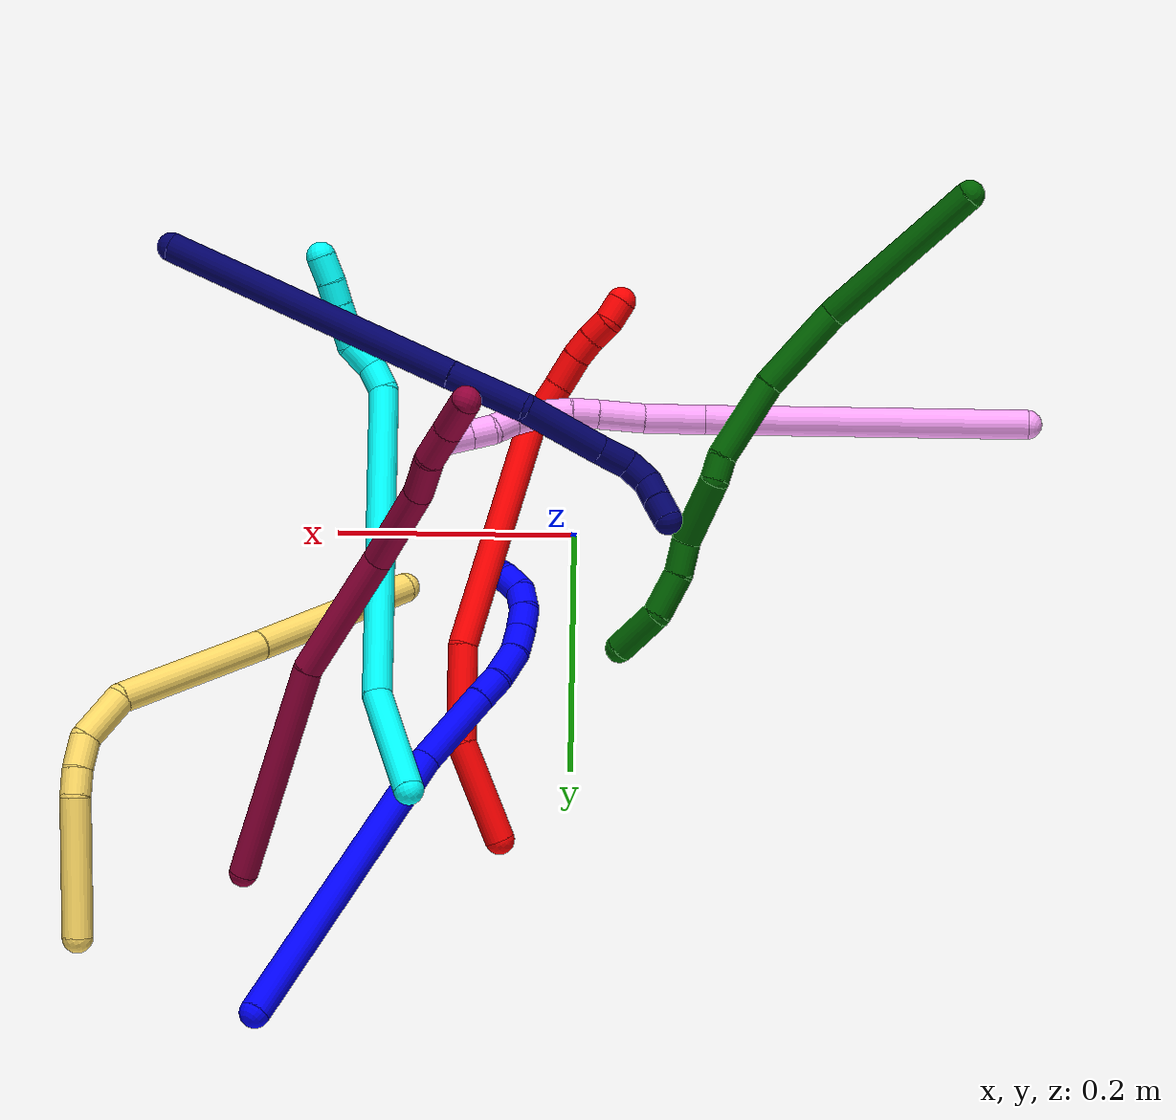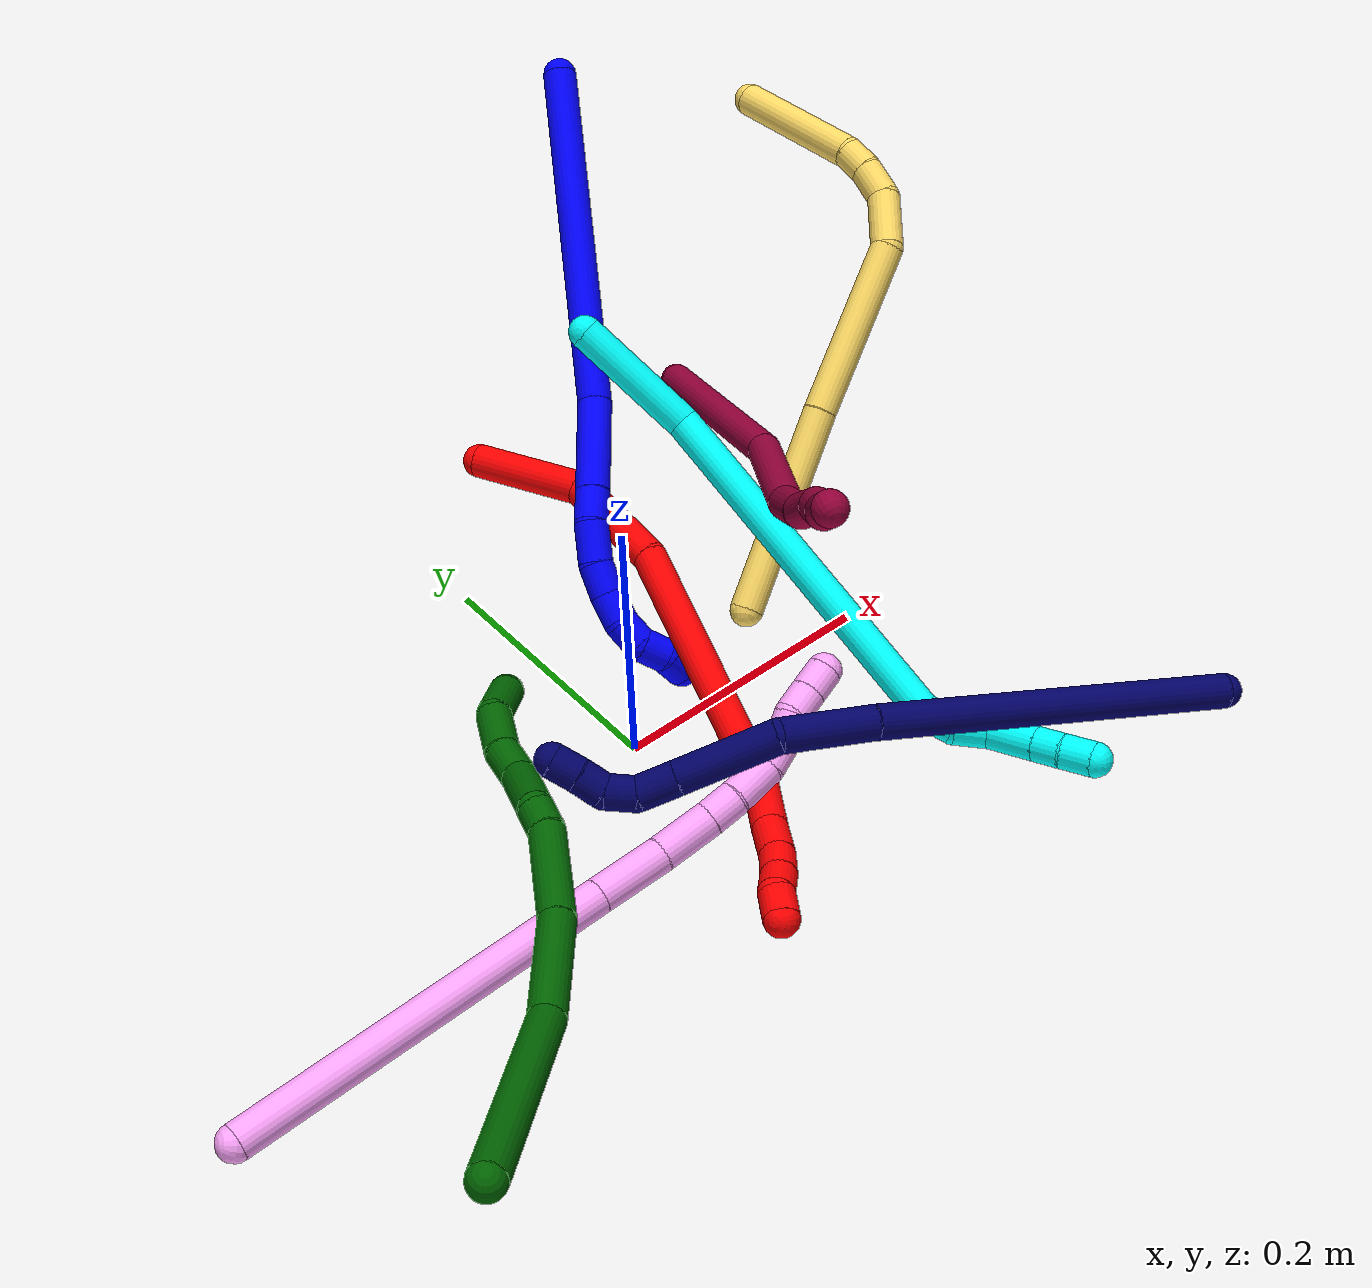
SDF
<sdf version="1.7">
 <world name="default">
  <plugin name="TubeGeneratorPlugin" filename="libtube_generator_plugin.so"/>
  <model name="photoneo_s_sensor">
   <static>1</static>
   <pose>0 0 2 1.57079 1.57079 3.14159</pose>
   <link name="link">
    <inertial><mass>0.1</mass></inertial>
    <sensor name="sensor" type="depth">
     <update_rate>30</update_rate>
     <camera>
      <horizontal_fov>1.22</horizontal_fov>
      <image><width>1920</width><height>1200</height><format>B8G8R8</format></image>
      <clip><near>0.1</near><far>4</far></clip>
      <depth_camera><output>points</output></depth_camera>
     </camera>
     <plugin name="camera_plugin" filename="libgazebo_ros_depth_camera.so">
      <baseline>0.2</baseline>
      <alwaysOn>1</alwaysOn>
      <updateRate>0.0</updateRate>
      <cameraName>camera_ir</cameraName>
      <imageTopicName>/camera/color/image_raw</imageTopicName>
      <cameraInfoTopicName>/camera/color/camera_info</cameraInfoTopicName>
      <depthImageTopicName>/camera/depth/image_raw</depthImageTopicName>
      <depthImageCameraInfoTopicName>/camera/depth/camera_info</depthImageCameraInfoTopicName>
      <pointCloudTopicName>/camera/depth/points</pointCloudTopicName>
      <frameName>fr_optical</frameName>
      <pointCloudCutoff>0.1</pointCloudCutoff>
      <pointCloudCutoffMax>2.0</pointCloudCutoffMax>
      <distortionK1>0</distortionK1>
      <distortionK2>0</distortionK2>
      <distortionK3>0</distortionK3>
      <distortionT1>0</distortionT1>
      <distortionT2>0</distortionT2>
      <CxPrime>0</CxPrime>
      <Cx>0</Cx>
      <Cy>0</Cy>
      <focalLength>0</focalLength>
      <hackBaseline>0</hackBaseline>
     </plugin>
    </sensor>
   </link>
  </model>
  <gravity>0 0 -9.8</gravity>
  <magnetic_field>6e-06 2.3e-05 -4.2e-05</magnetic_field>
  <atmosphere type="adiabatic"/>
  <physics name="default_physics" default="0" type="ode">
   <max_step_size>0.003</max_step_size>
   <real_time_factor>1</real_time_factor>
   <real_time_update_rate>1000</real_time_update_rate>
   <max_contacts>10000</max_contacts>
   <ode>
    <solver>
     <type>quick</type>
     <iters>100</iters>
     <sor>1.3</sor>
     <use_dynamic_moi_rescaling>0</use_dynamic_moi_rescaling>
    </solver>
    <constraints>
     <contact_max_correcting_vel>0</contact_max_correcting_vel>
     <contact_surface_layer>0.001</contact_surface_layer>
     <cfm>0</cfm>
     <erp>0.2</erp>
    </constraints>
   </ode>
  </physics>
  <scene><ambient>0.4 0.4 0.4 1</ambient><background>0.7 0.7 0.7 1</background><shadows>0</shadows></scene>
  <audio><device>default</device></audio>
  <spherical_coordinates>
   <surface_model>EARTH_WGS84</surface_model>
   <latitude_deg>0</latitude_deg>
   <longitude_deg>0</longitude_deg>
   <elevation>0</elevation>
   <heading_deg>0</heading_deg>
  </spherical_coordinates>
  <model name="bin">
   <static>1</static>
   <link name="bottom">
    <collision name="collision-bottom">
     <pose>0 0 -0.01 0 -0 0</pose>
     <geometry><box><size>0.8 0.6 0.02</size></box></geometry>
     <surface>
      <friction><ode><mu>100</mu><mu2>100</mu2></ode></friction>
      <contact><collide_bitmask>65535</collide_bitmask></contact>
     </surface>
    </collision>
   </link>
   <link name="west_wall">
    <collision name="collision-west_wall">
     <pose>-0.41 0 0.1 0 -0 0</pose>
     <geometry><box><size>0.02 0.6 0.2</size></box></geometry>
     <surface>
      <friction><ode><mu>100</mu><mu2>100</mu2></ode></friction>
      <contact><collide_bitmask>65535</collide_bitmask></contact>
     </surface>
    </collision>
   </link>
   <link name="east_wall">
    <collision name="collision-east_wall">
     <pose>0.41 0 0.1 0 -0 0</pose>
     <geometry><box><size>0.02 0.6 0.2</size></box></geometry>
     <surface>
      <friction><ode><mu>100</mu><mu2>100</mu2></ode></friction>
      <contact><collide_bitmask>65535</collide_bitmask></contact>
     </surface>
    </collision>
   </link>
   <link name="south_wall">
    <collision name="collision-south_wall">
     <pose>0 -0.31 0.1 0 -0 0</pose>
     <geometry><box><size>0.8 0.02 0.2</size></box></geometry>
     <surface>
      <friction><ode><mu>100</mu><mu2>100</mu2></ode></friction>
      <contact><collide_bitmask>65535</collide_bitmask></contact>
     </surface>
    </collision>
   </link>
   <link name="north_wall">
    <collision name="collision-north_wall">
     <pose>0 0.31 0.1 0 -0 0</pose>
     <geometry><box><size>0.8 0.02 0.2</size></box></geometry>
     <surface>
      <friction><ode><mu>100</mu><mu2>100</mu2></ode></friction>
      <contact><collide_bitmask>65535</collide_bitmask></contact>
     </surface>
    </collision>
   </link>
  </model>
  <model name="1">
   <static>0</static>
   <link name="1">
    <collision name="collision-cylinder-e_1_1_4">
     <pose>-0.006929 -0.001132 -0.133533 3.13311 -0.051844 -2.81745</pose>
     <geometry><cylinder><radius>0.0125</radius><length>0.267435</length></cylinder></geometry>
     <surface>
      <friction><ode><mu>1.16</mu><mu2>1.16</mu2><slip1>0</slip1><slip2>0</slip2></ode></friction>
      <contact><ode><kp>1e+06</kp><kd>1</kd><max_vel>0</max_vel><min_depth>0.001</min_depth></ode></contact>
     </surface>
    </collision>
    <visual name="visual-cylinder-e_1_1_4">
     <pose>-0.006929 -0.001132 -0.133533 3.13311 -0.051844 -2.81745</pose>
     <geometry><cylinder><radius>0.0125</radius><length>0.267435</length></cylinder></geometry>
     <material><ambient>0 0 1 1</ambient></material>
    </visual>
    <collision name="collision-cylinder-e_2_4_5">
     <pose>-0.017093 0.003114 -0.302254 -2.98992 -0.090601 1.07585</pose>
     <geometry><cylinder><radius>0.0125</radius><length>0.071485</length></cylinder></geometry>
     <surface>
      <friction><ode><mu>1.16</mu><mu2>1.16</mu2><slip1>0</slip1><slip2>0</slip2></ode></friction>
      <contact><ode><kp>1e+06</kp><kd>1</kd><max_vel>0</max_vel><min_depth>0.001</min_depth></ode></contact>
     </surface>
    </collision>
    <visual name="visual-cylinder-e_2_4_5">
     <pose>-0.017093 0.003114 -0.302254 -2.98992 -0.090601 1.07585</pose>
     <geometry><cylinder><radius>0.0125</radius><length>0.071485</length></cylinder></geometry>
     <material><ambient>0 0 1 1</ambient></material>
    </visual>
    <collision name="collision-cylinder-e_3_5_6">
     <pose>-0.020942 0.010312 -0.349431 -2.99099 -0.050726 0.648741</pose>
     <geometry><cylinder><radius>0.0125</radius><length>0.024286</length></cylinder></geometry>
     <surface>
      <friction><ode><mu>1.16</mu><mu2>1.16</mu2><slip1>0</slip1><slip2>0</slip2></ode></friction>
      <contact><ode><kp>1e+06</kp><kd>1</kd><max_vel>0</max_vel><min_depth>0.001</min_depth></ode></contact>
     </surface>
    </collision>
    <visual name="visual-cylinder-e_3_5_6">
     <pose>-0.020942 0.010312 -0.349431 -2.99099 -0.050726 0.648741</pose>
     <geometry><cylinder><radius>0.0125</radius><length>0.024286</length></cylinder></geometry>
     <material><ambient>0 0 1 1</ambient></material>
    </visual>
    <collision name="collision-cylinder-e_4_6_7">
     <pose>-0.021105 0.011157 -0.376634 3.07763 0.029693 0.869063</pose>
     <geometry><cylinder><radius>0.0125</radius><length>0.0305</length></cylinder></geometry>
     <surface>
      <friction><ode><mu>1.16</mu><mu2>1.16</mu2><slip1>0</slip1><slip2>0</slip2></ode></friction>
      <contact><ode><kp>1e+06</kp><kd>1</kd><max_vel>0</max_vel><min_depth>0.001</min_depth></ode></contact>
     </surface>
    </collision>
    <visual name="visual-cylinder-e_4_6_7">
     <pose>-0.021105 0.011157 -0.376634 3.07763 0.029693 0.869063</pose>
     <geometry><cylinder><radius>0.0125</radius><length>0.0305</length></cylinder></geometry>
     <material><ambient>0 0 1 1</ambient></material>
    </visual>
    <collision name="collision-cylinder-e_5_7_8">
     <pose>-0.021077 0.006591 -0.402961 2.82909 -0.036354 -0.229777</pose>
     <geometry><cylinder><radius>0.0125</radius><length>0.023377</length></cylinder></geometry>
     <surface>
      <friction><ode><mu>1.16</mu><mu2>1.16</mu2><slip1>0</slip1><slip2>0</slip2></ode></friction>
      <contact><ode><kp>1e+06</kp><kd>1</kd><max_vel>0</max_vel><min_depth>0.001</min_depth></ode></contact>
     </surface>
    </collision>
    <visual name="visual-cylinder-e_5_7_8">
     <pose>-0.021077 0.006591 -0.402961 2.82909 -0.036354 -0.229777</pose>
     <geometry><cylinder><radius>0.0125</radius><length>0.023377</length></cylinder></geometry>
     <material><ambient>0 0 1 1</ambient></material>
    </visual>
    <collision name="collision-cylinder-e_6_8_9">
     <pose>-0.02314 -0.00082 -0.424156 2.77935 -0.150813 -0.78255</pose>
     <geometry><cylinder><radius>0.0125</radius><length>0.021806</length></cylinder></geometry>
     <surface>
      <friction><ode><mu>1.16</mu><mu2>1.16</mu2><slip1>0</slip1><slip2>0</slip2></ode></friction>
      <contact><ode><kp>1e+06</kp><kd>1</kd><max_vel>0</max_vel><min_depth>0.001</min_depth></ode></contact>
     </surface>
    </collision>
    <visual name="visual-cylinder-e_6_8_9">
     <pose>-0.02314 -0.00082 -0.424156 2.77935 -0.150813 -0.78255</pose>
     <geometry><cylinder><radius>0.0125</radius><length>0.021806</length></cylinder></geometry>
     <material><ambient>0 0 1 1</ambient></material>
    </visual>
    <collision name="collision-cylinder-e_7_9_10">
     <pose>-0.026185 -0.010979 -0.441958 2.45425 -0.139893 -0.38665</pose>
     <geometry><cylinder><radius>0.0125</radius><length>0.020181</length></cylinder></geometry>
     <surface>
      <friction><ode><mu>1.16</mu><mu2>1.16</mu2><slip1>0</slip1><slip2>0</slip2></ode></friction>
      <contact><ode><kp>1e+06</kp><kd>1</kd><max_vel>0</max_vel><min_depth>0.001</min_depth></ode></contact>
     </surface>
    </collision>
    <visual name="visual-cylinder-e_7_9_10">
     <pose>-0.026185 -0.010979 -0.441958 2.45425 -0.139893 -0.38665</pose>
     <geometry><cylinder><radius>0.0125</radius><length>0.020181</length></cylinder></geometry>
     <material><ambient>0 0 1 1</ambient></material>
    </visual>
    <collision name="collision-cylinder-e_8_10_11">
     <pose>-0.02837 -0.026939 -0.453546 1.95273 -0.074853 -0.11067</pose>
     <geometry><cylinder><radius>0.0125</radius><length>0.020792</length></cylinder></geometry>
     <surface>
      <friction><ode><mu>1.16</mu><mu2>1.16</mu2><slip1>0</slip1><slip2>0</slip2></ode></friction>
      <contact><ode><kp>1e+06</kp><kd>1</kd><max_vel>0</max_vel><min_depth>0.001</min_depth></ode></contact>
     </surface>
    </collision>
    <visual name="visual-cylinder-e_8_10_11">
     <pose>-0.02837 -0.026939 -0.453546 1.95273 -0.074853 -0.11067</pose>
     <geometry><cylinder><radius>0.0125</radius><length>0.020792</length></cylinder></geometry>
     <material><ambient>0 0 1 1</ambient></material>
    </visual>
    <collision name="collision-cylinder-e_9_11_2">
     <pose>-0.025831 -0.045242 -0.46128 1.99012 0.335649 0.510626</pose>
     <geometry><cylinder><radius>0.0125</radius><length>0.020137</length></cylinder></geometry>
     <surface>
      <friction><ode><mu>1.16</mu><mu2>1.16</mu2><slip1>0</slip1><slip2>0</slip2></ode></friction>
      <contact><ode><kp>1e+06</kp><kd>1</kd><max_vel>0</max_vel><min_depth>0.001</min_depth></ode></contact>
     </surface>
    </collision>
    <visual name="visual-cylinder-e_9_11_2">
     <pose>-0.025831 -0.045242 -0.46128 1.99012 0.335649 0.510626</pose>
     <geometry><cylinder><radius>0.0125</radius><length>0.020137</length></cylinder></geometry>
     <material><ambient>0 0 1 1</ambient></material>
    </visual>
    <collision name="collision-sphere-2">
     <pose>-0.022514 -0.053925 -0.465151 0 -0 0</pose>
     <geometry><sphere><radius>0.0125</radius></sphere></geometry>
     <surface>
      <friction><ode><mu>1.16</mu><mu2>1.16</mu2><slip1>0</slip1><slip2>0</slip2></ode></friction>
      <contact><ode><kp>1e+06</kp><kd>1</kd><max_vel>0</max_vel><min_depth>0.001</min_depth></ode></contact>
     </surface>
    </collision>
    <visual name="visual-sphere-2">
     <pose>-0.022514 -0.053925 -0.465151 0 -0 0</pose>
     <geometry><sphere><radius>0.0125</radius></sphere></geometry>
     <material><ambient>0 0 1 1</ambient></material>
    </visual>
    <collision name="collision-sphere-11">
     <pose>-0.029147 -0.036559 -0.45741 0 -0 0</pose>
     <geometry><sphere><radius>0.0125</radius></sphere></geometry>
     <surface>
      <friction><ode><mu>1.16</mu><mu2>1.16</mu2><slip1>0</slip1><slip2>0</slip2></ode></friction>
      <contact><ode><kp>1e+06</kp><kd>1</kd><max_vel>0</max_vel><min_depth>0.001</min_depth></ode></contact>
     </surface>
    </collision>
    <visual name="visual-sphere-11">
     <pose>-0.029147 -0.036559 -0.45741 0 -0 0</pose>
     <geometry><sphere><radius>0.0125</radius></sphere></geometry>
     <material><ambient>0 0 1 1</ambient></material>
    </visual>
    <collision name="collision-sphere-10">
     <pose>-0.027592 -0.017319 -0.449682 0 -0 0</pose>
     <geometry><sphere><radius>0.0125</radius></sphere></geometry>
     <surface>
      <friction><ode><mu>1.16</mu><mu2>1.16</mu2><slip1>0</slip1><slip2>0</slip2></ode></friction>
      <contact><ode><kp>1e+06</kp><kd>1</kd><max_vel>0</max_vel><min_depth>0.001</min_depth></ode></contact>
     </surface>
    </collision>
    <visual name="visual-sphere-10">
     <pose>-0.027592 -0.017319 -0.449682 0 -0 0</pose>
     <geometry><sphere><radius>0.0125</radius></sphere></geometry>
     <material><ambient>0 0 1 1</ambient></material>
    </visual>
    <collision name="collision-sphere-9">
     <pose>-0.024778 -0.00464 -0.434235 0 -0 0</pose>
     <geometry><sphere><radius>0.0125</radius></sphere></geometry>
     <surface>
      <friction><ode><mu>1.16</mu><mu2>1.16</mu2><slip1>0</slip1><slip2>0</slip2></ode></friction>
      <contact><ode><kp>1e+06</kp><kd>1</kd><max_vel>0</max_vel><min_depth>0.001</min_depth></ode></contact>
     </surface>
    </collision>
    <visual name="visual-sphere-9">
     <pose>-0.024778 -0.00464 -0.434235 0 -0 0</pose>
     <geometry><sphere><radius>0.0125</radius></sphere></geometry>
     <material><ambient>0 0 1 1</ambient></material>
    </visual>
    <collision name="collision-sphere-4">
     <pose>-0.013859 -0.002264 -0.267066 0 -0 0</pose>
     <geometry><sphere><radius>0.0125</radius></sphere></geometry>
     <surface>
      <friction><ode><mu>1.16</mu><mu2>1.16</mu2><slip1>0</slip1><slip2>0</slip2></ode></friction>
      <contact><ode><kp>1e+06</kp><kd>1</kd><max_vel>0</max_vel><min_depth>0.001</min_depth></ode></contact>
     </surface>
    </collision>
    <visual name="visual-sphere-4">
     <pose>-0.013859 -0.002264 -0.267066 0 -0 0</pose>
     <geometry><sphere><radius>0.0125</radius></sphere></geometry>
     <material><ambient>0 0 1 1</ambient></material>
    </visual>
    <collision name="collision-sphere-1">
     <geometry><sphere><radius>0.0125</radius></sphere></geometry>
     <surface>
      <friction><ode><mu>1.16</mu><mu2>1.16</mu2><slip1>0</slip1><slip2>0</slip2></ode></friction>
      <contact><ode><kp>1e+06</kp><kd>1</kd><max_vel>0</max_vel><min_depth>0.001</min_depth></ode></contact>
     </surface>
    </collision>
    <visual name="visual-sphere-1">
     <geometry><sphere><radius>0.0125</radius></sphere></geometry>
     <material><ambient>0 0 1 1</ambient></material>
    </visual>
    <collision name="collision-sphere-8">
     <pose>-0.021502 0.003 -0.414076 0 -0 0</pose>
     <geometry><sphere><radius>0.0125</radius></sphere></geometry>
     <surface>
      <friction><ode><mu>1.16</mu><mu2>1.16</mu2><slip1>0</slip1><slip2>0</slip2></ode></friction>
      <contact><ode><kp>1e+06</kp><kd>1</kd><max_vel>0</max_vel><min_depth>0.001</min_depth></ode></contact>
     </surface>
    </collision>
    <visual name="visual-sphere-8">
     <pose>-0.021502 0.003 -0.414076 0 -0 0</pose>
     <geometry><sphere><radius>0.0125</radius></sphere></geometry>
     <material><ambient>0 0 1 1</ambient></material>
    </visual>
    <collision name="collision-sphere-5">
     <pose>-0.020327 0.008492 -0.337441 0 -0 0</pose>
     <geometry><sphere><radius>0.0125</radius></sphere></geometry>
     <surface>
      <friction><ode><mu>1.16</mu><mu2>1.16</mu2><slip1>0</slip1><slip2>0</slip2></ode></friction>
      <contact><ode><kp>1e+06</kp><kd>1</kd><max_vel>0</max_vel><min_depth>0.001</min_depth></ode></contact>
     </surface>
    </collision>
    <visual name="visual-sphere-5">
     <pose>-0.020327 0.008492 -0.337441 0 -0 0</pose>
     <geometry><sphere><radius>0.0125</radius></sphere></geometry>
     <material><ambient>0 0 1 1</ambient></material>
    </visual>
    <collision name="collision-sphere-6">
     <pose>-0.021558 0.012131 -0.361421 0 -0 0</pose>
     <geometry><sphere><radius>0.0125</radius></sphere></geometry>
     <surface>
      <friction><ode><mu>1.16</mu><mu2>1.16</mu2><slip1>0</slip1><slip2>0</slip2></ode></friction>
      <contact><ode><kp>1e+06</kp><kd>1</kd><max_vel>0</max_vel><min_depth>0.001</min_depth></ode></contact>
     </surface>
    </collision>
    <visual name="visual-sphere-6">
     <pose>-0.021558 0.012131 -0.361421 0 -0 0</pose>
     <geometry><sphere><radius>0.0125</radius></sphere></geometry>
     <material><ambient>0 0 1 1</ambient></material>
    </visual>
    <collision name="collision-sphere-7">
     <pose>-0.020652 0.010183 -0.391846 0 -0 0</pose>
     <geometry><sphere><radius>0.0125</radius></sphere></geometry>
     <surface>
      <friction><ode><mu>1.16</mu><mu2>1.16</mu2><slip1>0</slip1><slip2>0</slip2></ode></friction>
      <contact><ode><kp>1e+06</kp><kd>1</kd><max_vel>0</max_vel><min_depth>0.001</min_depth></ode></contact>
     </surface>
    </collision>
    <visual name="visual-sphere-7">
     <pose>-0.020652 0.010183 -0.391846 0 -0 0</pose>
     <geometry><sphere><radius>0.0125</radius></sphere></geometry>
     <material><ambient>0 0 1 1</ambient></material>
    </visual>
    <inertial>
     <pose>-0.013726 -0.002092 -0.247198 0 -0 0</pose>
     <mass>0.5</mass>
     <inertia>
      <ixx>-0.001972</ixx>
      <ixy>0</ixy>
      <ixz>0</ixz>
      <iyy>0.001014</iyy>
      <iyz>0</iyz>
      <izz>6.3e-05</izz>
     </inertia>
    </inertial>
   </link>
   <pose>0.244067 0.379338 0.269303 0.677601 0.80687 1.79433</pose>
  </model>
  <model name="2">
   <static>0</static>
   <link name="2">
    <collision name="collision-cylinder-e_1_1_4">
     <pose>-0.034542 -0.026844 1e-06 1.57075 -0.910153 -0.910114</pose>
     <geometry><cylinder><radius>0.0125</radius><length>0.087492</length></cylinder></geometry>
     <surface>
      <friction><ode><mu>1.16</mu><mu2>1.16</mu2><slip1>0</slip1><slip2>0</slip2></ode></friction>
      <contact><ode><kp>1e+06</kp><kd>1</kd><max_vel>0</max_vel><min_depth>0.001</min_depth></ode></contact>
     </surface>
    </collision>
    <visual name="visual-cylinder-e_1_1_4">
     <pose>-0.034542 -0.026844 1e-06 1.57075 -0.910153 -0.910114</pose>
     <geometry><cylinder><radius>0.0125</radius><length>0.087492</length></cylinder></geometry>
     <material><ambient>1 0 0 1</ambient></material>
    </visual>
    <collision name="collision-cylinder-e_2_4_5">
     <pose>-0.088013 -0.089125 -0.006557 1.75382 -0.483638 -0.576465</pose>
     <geometry><cylinder><radius>0.0125</radius><length>0.081418</length></cylinder></geometry>
     <surface>
      <friction><ode><mu>1.16</mu><mu2>1.16</mu2><slip1>0</slip1><slip2>0</slip2></ode></friction>
      <contact><ode><kp>1e+06</kp><kd>1</kd><max_vel>0</max_vel><min_depth>0.001</min_depth></ode></contact>
     </surface>
    </collision>
    <visual name="visual-cylinder-e_2_4_5">
     <pose>-0.088013 -0.089125 -0.006557 1.75382 -0.483638 -0.576465</pose>
     <geometry><cylinder><radius>0.0125</radius><length>0.081418</length></cylinder></geometry>
     <material><ambient>1 0 0 1</ambient></material>
    </visual>
    <collision name="collision-cylinder-e_3_5_6">
     <pose>-0.126723 -0.217084 -0.040199 1.85556 -0.202374 -0.269388</pose>
     <geometry><cylinder><radius>0.0125</radius><length>0.196824</length></cylinder></geometry>
     <surface>
      <friction><ode><mu>1.16</mu><mu2>1.16</mu2><slip1>0</slip1><slip2>0</slip2></ode></friction>
      <contact><ode><kp>1e+06</kp><kd>1</kd><max_vel>0</max_vel><min_depth>0.001</min_depth></ode></contact>
     </surface>
    </collision>
    <visual name="visual-cylinder-e_3_5_6">
     <pose>-0.126723 -0.217084 -0.040199 1.85556 -0.202374 -0.269388</pose>
     <geometry><cylinder><radius>0.0125</radius><length>0.196824</length></cylinder></geometry>
     <material><ambient>1 0 0 1</ambient></material>
    </visual>
    <collision name="collision-cylinder-e_4_6_7">
     <pose>-0.150235 -0.325929 -0.082011 2.3049 -0.168106 -0.374566</pose>
     <geometry><cylinder><radius>0.0125</radius><length>0.044602</length></cylinder></geometry>
     <surface>
      <friction><ode><mu>1.16</mu><mu2>1.16</mu2><slip1>0</slip1><slip2>0</slip2></ode></friction>
      <contact><ode><kp>1e+06</kp><kd>1</kd><max_vel>0</max_vel><min_depth>0.001</min_depth></ode></contact>
     </surface>
    </collision>
    <visual name="visual-cylinder-e_4_6_7">
     <pose>-0.150235 -0.325929 -0.082011 2.3049 -0.168106 -0.374566</pose>
     <geometry><cylinder><radius>0.0125</radius><length>0.044602</length></cylinder></geometry>
     <material><ambient>1 0 0 1</ambient></material>
    </visual>
    <collision name="collision-cylinder-e_5_7_8">
     <pose>-0.157329 -0.351873 -0.106668 2.3719 -0.238616 -0.575495</pose>
     <geometry><cylinder><radius>0.0125</radius><length>0.028455</length></cylinder></geometry>
     <surface>
      <friction><ode><mu>1.16</mu><mu2>1.16</mu2><slip1>0</slip1><slip2>0</slip2></ode></friction>
      <contact><ode><kp>1e+06</kp><kd>1</kd><max_vel>0</max_vel><min_depth>0.001</min_depth></ode></contact>
     </surface>
    </collision>
    <visual name="visual-cylinder-e_5_7_8">
     <pose>-0.157329 -0.351873 -0.106668 2.3719 -0.238616 -0.575495</pose>
     <geometry><cylinder><radius>0.0125</radius><length>0.028455</length></cylinder></geometry>
     <material><ambient>1 0 0 1</ambient></material>
    </visual>
    <collision name="collision-cylinder-e_6_8_9">
     <pose>-0.162292 -0.367848 -0.124683 2.47566 -0.154381 -0.440041</pose>
     <geometry><cylinder><radius>0.0125</radius><length>0.020817</length></cylinder></geometry>
     <surface>
      <friction><ode><mu>1.16</mu><mu2>1.16</mu2><slip1>0</slip1><slip2>0</slip2></ode></friction>
      <contact><ode><kp>1e+06</kp><kd>1</kd><max_vel>0</max_vel><min_depth>0.001</min_depth></ode></contact>
     </surface>
    </collision>
    <visual name="visual-cylinder-e_6_8_9">
     <pose>-0.162292 -0.367848 -0.124683 2.47566 -0.154381 -0.440041</pose>
     <geometry><cylinder><radius>0.0125</radius><length>0.020817</length></cylinder></geometry>
     <material><ambient>1 0 0 1</ambient></material>
    </visual>
    <collision name="collision-cylinder-e_7_9_10">
     <pose>-0.16468 -0.379373 -0.141469 2.60524 -0.077609 -0.280708</pose>
     <geometry><cylinder><radius>0.0125</radius><length>0.020301</length></cylinder></geometry>
     <surface>
      <friction><ode><mu>1.16</mu><mu2>1.16</mu2><slip1>0</slip1><slip2>0</slip2></ode></friction>
      <contact><ode><kp>1e+06</kp><kd>1</kd><max_vel>0</max_vel><min_depth>0.001</min_depth></ode></contact>
     </surface>
    </collision>
    <visual name="visual-cylinder-e_7_9_10">
     <pose>-0.16468 -0.379373 -0.141469 2.60524 -0.077609 -0.280708</pose>
     <geometry><cylinder><radius>0.0125</radius><length>0.020301</length></cylinder></geometry>
     <material><ambient>1 0 0 1</ambient></material>
    </visual>
    <collision name="collision-cylinder-e_8_10_2">
     <pose>-0.166394 -0.392875 -0.155705 2.15738 -0.092477 -0.172197</pose>
     <geometry><cylinder><radius>0.0125</radius><length>0.020091</length></cylinder></geometry>
     <surface>
      <friction><ode><mu>1.16</mu><mu2>1.16</mu2><slip1>0</slip1><slip2>0</slip2></ode></friction>
      <contact><ode><kp>1e+06</kp><kd>1</kd><max_vel>0</max_vel><min_depth>0.001</min_depth></ode></contact>
     </surface>
    </collision>
    <visual name="visual-cylinder-e_8_10_2">
     <pose>-0.166394 -0.392875 -0.155705 2.15738 -0.092477 -0.172197</pose>
     <geometry><cylinder><radius>0.0125</radius><length>0.020091</length></cylinder></geometry>
     <material><ambient>1 0 0 1</ambient></material>
    </visual>
    <collision name="collision-sphere-2">
     <pose>-0.167322 -0.401206 -0.161241 0 -0 0</pose>
     <geometry><sphere><radius>0.0125</radius></sphere></geometry>
     <surface>
      <friction><ode><mu>1.16</mu><mu2>1.16</mu2><slip1>0</slip1><slip2>0</slip2></ode></friction>
      <contact><ode><kp>1e+06</kp><kd>1</kd><max_vel>0</max_vel><min_depth>0.001</min_depth></ode></contact>
     </surface>
    </collision>
    <visual name="visual-sphere-2">
     <pose>-0.167322 -0.401206 -0.161241 0 -0 0</pose>
     <geometry><sphere><radius>0.0125</radius></sphere></geometry>
     <material><ambient>1 0 0 1</ambient></material>
    </visual>
    <collision name="collision-sphere-10">
     <pose>-0.165467 -0.384544 -0.150168 0 -0 0</pose>
     <geometry><sphere><radius>0.0125</radius></sphere></geometry>
     <surface>
      <friction><ode><mu>1.16</mu><mu2>1.16</mu2><slip1>0</slip1><slip2>0</slip2></ode></friction>
      <contact><ode><kp>1e+06</kp><kd>1</kd><max_vel>0</max_vel><min_depth>0.001</min_depth></ode></contact>
     </surface>
    </collision>
    <visual name="visual-sphere-10">
     <pose>-0.165467 -0.384544 -0.150168 0 -0 0</pose>
     <geometry><sphere><radius>0.0125</radius></sphere></geometry>
     <material><ambient>1 0 0 1</ambient></material>
    </visual>
    <collision name="collision-sphere-9">
     <pose>-0.163893 -0.374202 -0.13277 0 -0 0</pose>
     <geometry><sphere><radius>0.0125</radius></sphere></geometry>
     <surface>
      <friction><ode><mu>1.16</mu><mu2>1.16</mu2><slip1>0</slip1><slip2>0</slip2></ode></friction>
      <contact><ode><kp>1e+06</kp><kd>1</kd><max_vel>0</max_vel><min_depth>0.001</min_depth></ode></contact>
     </surface>
    </collision>
    <visual name="visual-sphere-9">
     <pose>-0.163893 -0.374202 -0.13277 0 -0 0</pose>
     <geometry><sphere><radius>0.0125</radius></sphere></geometry>
     <material><ambient>1 0 0 1</ambient></material>
    </visual>
    <collision name="collision-sphere-4">
     <pose>-0.069083 -0.053687 3e-06 0 -0 0</pose>
     <geometry><sphere><radius>0.0125</radius></sphere></geometry>
     <surface>
      <friction><ode><mu>1.16</mu><mu2>1.16</mu2><slip1>0</slip1><slip2>0</slip2></ode></friction>
      <contact><ode><kp>1e+06</kp><kd>1</kd><max_vel>0</max_vel><min_depth>0.001</min_depth></ode></contact>
     </surface>
    </collision>
    <visual name="visual-sphere-4">
     <pose>-0.069083 -0.053687 3e-06 0 -0 0</pose>
     <geometry><sphere><radius>0.0125</radius></sphere></geometry>
     <material><ambient>1 0 0 1</ambient></material>
    </visual>
    <collision name="collision-sphere-1">
     <geometry><sphere><radius>0.0125</radius></sphere></geometry>
     <surface>
      <friction><ode><mu>1.16</mu><mu2>1.16</mu2><slip1>0</slip1><slip2>0</slip2></ode></friction>
      <contact><ode><kp>1e+06</kp><kd>1</kd><max_vel>0</max_vel><min_depth>0.001</min_depth></ode></contact>
     </surface>
    </collision>
    <visual name="visual-sphere-1">
     <geometry><sphere><radius>0.0125</radius></sphere></geometry>
     <material><ambient>1 0 0 1</ambient></material>
    </visual>
    <collision name="collision-sphere-8">
     <pose>-0.160692 -0.361494 -0.116596 0 -0 0</pose>
     <geometry><sphere><radius>0.0125</radius></sphere></geometry>
     <surface>
      <friction><ode><mu>1.16</mu><mu2>1.16</mu2><slip1>0</slip1><slip2>0</slip2></ode></friction>
      <contact><ode><kp>1e+06</kp><kd>1</kd><max_vel>0</max_vel><min_depth>0.001</min_depth></ode></contact>
     </surface>
    </collision>
    <visual name="visual-sphere-8">
     <pose>-0.160692 -0.361494 -0.116596 0 -0 0</pose>
     <geometry><sphere><radius>0.0125</radius></sphere></geometry>
     <material><ambient>1 0 0 1</ambient></material>
    </visual>
    <collision name="collision-sphere-5">
     <pose>-0.106943 -0.124563 -0.013117 0 -0 0</pose>
     <geometry><sphere><radius>0.0125</radius></sphere></geometry>
     <surface>
      <friction><ode><mu>1.16</mu><mu2>1.16</mu2><slip1>0</slip1><slip2>0</slip2></ode></friction>
      <contact><ode><kp>1e+06</kp><kd>1</kd><max_vel>0</max_vel><min_depth>0.001</min_depth></ode></contact>
     </surface>
    </collision>
    <visual name="visual-sphere-5">
     <pose>-0.106943 -0.124563 -0.013117 0 -0 0</pose>
     <geometry><sphere><radius>0.0125</radius></sphere></geometry>
     <material><ambient>1 0 0 1</ambient></material>
    </visual>
    <collision name="collision-sphere-6">
     <pose>-0.146503 -0.309606 -0.067281 0 -0 0</pose>
     <geometry><sphere><radius>0.0125</radius></sphere></geometry>
     <surface>
      <friction><ode><mu>1.16</mu><mu2>1.16</mu2><slip1>0</slip1><slip2>0</slip2></ode></friction>
      <contact><ode><kp>1e+06</kp><kd>1</kd><max_vel>0</max_vel><min_depth>0.001</min_depth></ode></contact>
     </surface>
    </collision>
    <visual name="visual-sphere-6">
     <pose>-0.146503 -0.309606 -0.067281 0 -0 0</pose>
     <geometry><sphere><radius>0.0125</radius></sphere></geometry>
     <material><ambient>1 0 0 1</ambient></material>
    </visual>
    <collision name="collision-sphere-7">
     <pose>-0.153966 -0.342253 -0.09674 0 -0 0</pose>
     <geometry><sphere><radius>0.0125</radius></sphere></geometry>
     <surface>
      <friction><ode><mu>1.16</mu><mu2>1.16</mu2><slip1>0</slip1><slip2>0</slip2></ode></friction>
      <contact><ode><kp>1e+06</kp><kd>1</kd><max_vel>0</max_vel><min_depth>0.001</min_depth></ode></contact>
     </surface>
    </collision>
    <visual name="visual-sphere-7">
     <pose>-0.153966 -0.342253 -0.09674 0 -0 0</pose>
     <geometry><sphere><radius>0.0125</radius></sphere></geometry>
     <material><ambient>1 0 0 1</ambient></material>
    </visual>
    <inertial>
     <pose>-0.112745 -0.200269 -0.04747 0 -0 0</pose>
     <mass>0.5</mass>
     <inertia>
      <ixx>0.000442</ixx>
      <ixy>0</ixy>
      <ixz>0</ixz>
      <iyy>-0.000367</iyy>
      <iyz>0</iyz>
      <izz>0.000883</izz>
     </inertia>
    </inertial>
   </link>
   <pose>0.058073 0.254171 0.068814 2.39393 0.571147 2.42746</pose>
  </model>
  <model name="3">
   <static>0</static>
   <link name="3">
    <collision name="collision-cylinder-e_1_1_4">
     <pose>0.033903 -0.032046 0.011783 1.21844 0.781851 0.560034</pose>
     <geometry><cylinder><radius>0.0125</radius><length>0.096233</length></cylinder></geometry>
     <surface>
      <friction><ode><mu>1.16</mu><mu2>1.16</mu2><slip1>0</slip1><slip2>0</slip2></ode></friction>
      <contact><ode><kp>1e+06</kp><kd>1</kd><max_vel>0</max_vel><min_depth>0.001</min_depth></ode></contact>
     </surface>
    </collision>
    <visual name="visual-cylinder-e_1_1_4">
     <pose>0.033903 -0.032046 0.011783 1.21844 0.781851 0.560034</pose>
     <geometry><cylinder><radius>0.0125</radius><length>0.096233</length></cylinder></geometry>
     <material><ambient>0.003922 1 0.996078 1</ambient></material>
    </visual>
    <collision name="collision-cylinder-e_2_4_5">
     <pose>0.164852 -0.159319 0.005103 1.76232 0.785638 0.931153</pose>
     <geometry><cylinder><radius>0.0125</radius><length>0.274423</length></cylinder></geometry>
     <surface>
      <friction><ode><mu>1.16</mu><mu2>1.16</mu2><slip1>0</slip1><slip2>0</slip2></ode></friction>
      <contact><ode><kp>1e+06</kp><kd>1</kd><max_vel>0</max_vel><min_depth>0.001</min_depth></ode></contact>
     </surface>
    </collision>
    <visual name="visual-cylinder-e_2_4_5">
     <pose>0.164852 -0.159319 0.005103 1.76232 0.785638 0.931153</pose>
     <geometry><cylinder><radius>0.0125</radius><length>0.274423</length></cylinder></geometry>
     <material><ambient>0.003922 1 0.996078 1</ambient></material>
    </visual>
    <collision name="collision-cylinder-e_3_5_6">
     <pose>0.267982 -0.264709 -0.010678 1.31261 0.524642 0.407862</pose>
     <geometry><cylinder><radius>0.0125</radius><length>0.02429</length></cylinder></geometry>
     <surface>
      <friction><ode><mu>1.16</mu><mu2>1.16</mu2><slip1>0</slip1><slip2>0</slip2></ode></friction>
      <contact><ode><kp>1e+06</kp><kd>1</kd><max_vel>0</max_vel><min_depth>0.001</min_depth></ode></contact>
     </surface>
    </collision>
    <visual name="visual-cylinder-e_3_5_6">
     <pose>0.267982 -0.264709 -0.010678 1.31261 0.524642 0.407862</pose>
     <geometry><cylinder><radius>0.0125</radius><length>0.02429</length></cylinder></geometry>
     <material><ambient>0.003922 1 0.996078 1</ambient></material>
    </visual>
    <collision name="collision-cylinder-e_4_6_7">
     <pose>0.275786 -0.286826 -0.003725 1.22779 0.134731 0.095022</pose>
     <geometry><cylinder><radius>0.0125</radius><length>0.02562</length></cylinder></geometry>
     <surface>
      <friction><ode><mu>1.16</mu><mu2>1.16</mu2><slip1>0</slip1><slip2>0</slip2></ode></friction>
      <contact><ode><kp>1e+06</kp><kd>1</kd><max_vel>0</max_vel><min_depth>0.001</min_depth></ode></contact>
     </surface>
    </collision>
    <visual name="visual-cylinder-e_4_6_7">
     <pose>0.275786 -0.286826 -0.003725 1.22779 0.134731 0.095022</pose>
     <geometry><cylinder><radius>0.0125</radius><length>0.02562</length></cylinder></geometry>
     <material><ambient>0.003922 1 0.996078 1</ambient></material>
    </visual>
    <collision name="collision-cylinder-e_5_7_8">
     <pose>0.280242 -0.316523 -0.002294 1.72946 0.151092 0.177064</pose>
     <geometry><cylinder><radius>0.0125</radius><length>0.036349</length></cylinder></geometry>
     <surface>
      <friction><ode><mu>1.16</mu><mu2>1.16</mu2><slip1>0</slip1><slip2>0</slip2></ode></friction>
      <contact><ode><kp>1e+06</kp><kd>1</kd><max_vel>0</max_vel><min_depth>0.001</min_depth></ode></contact>
     </surface>
    </collision>
    <visual name="visual-cylinder-e_5_7_8">
     <pose>0.280242 -0.316523 -0.002294 1.72946 0.151092 0.177064</pose>
     <geometry><cylinder><radius>0.0125</radius><length>0.036349</length></cylinder></geometry>
     <material><ambient>0.003922 1 0.996078 1</ambient></material>
    </visual>
    <collision name="collision-cylinder-e_6_8_9">
     <pose>0.284364 -0.344058 -0.006987 1.75785 0.138187 0.166673</pose>
     <geometry><cylinder><radius>0.0125</radius><length>0.020128</length></cylinder></geometry>
     <surface>
      <friction><ode><mu>1.16</mu><mu2>1.16</mu2><slip1>0</slip1><slip2>0</slip2></ode></friction>
      <contact><ode><kp>1e+06</kp><kd>1</kd><max_vel>0</max_vel><min_depth>0.001</min_depth></ode></contact>
     </surface>
    </collision>
    <visual name="visual-cylinder-e_6_8_9">
     <pose>0.284364 -0.344058 -0.006987 1.75785 0.138187 0.166673</pose>
     <geometry><cylinder><radius>0.0125</radius><length>0.020128</length></cylinder></geometry>
     <material><ambient>0.003922 1 0.996078 1</ambient></material>
    </visual>
    <collision name="collision-cylinder-e_7_9_2">
     <pose>0.287671 -0.365129 -0.009786 1.65449 0.168089 0.182701</pose>
     <geometry><cylinder><radius>0.0125</radius><length>0.022957</length></cylinder></geometry>
     <surface>
      <friction><ode><mu>1.16</mu><mu2>1.16</mu2><slip1>0</slip1><slip2>0</slip2></ode></friction>
      <contact><ode><kp>1e+06</kp><kd>1</kd><max_vel>0</max_vel><min_depth>0.001</min_depth></ode></contact>
     </surface>
    </collision>
    <visual name="visual-cylinder-e_7_9_2">
     <pose>0.287671 -0.365129 -0.009786 1.65449 0.168089 0.182701</pose>
     <geometry><cylinder><radius>0.0125</radius><length>0.022957</length></cylinder></geometry>
     <material><ambient>0.003922 1 0.996078 1</ambient></material>
    </visual>
    <collision name="collision-sphere-2">
     <pose>0.289591 -0.376406 -0.010732 0 -0 0</pose>
     <geometry><sphere><radius>0.0125</radius></sphere></geometry>
     <surface>
      <friction><ode><mu>1.16</mu><mu2>1.16</mu2><slip1>0</slip1><slip2>0</slip2></ode></friction>
      <contact><ode><kp>1e+06</kp><kd>1</kd><max_vel>0</max_vel><min_depth>0.001</min_depth></ode></contact>
     </surface>
    </collision>
    <visual name="visual-sphere-2">
     <pose>0.289591 -0.376406 -0.010732 0 -0 0</pose>
     <geometry><sphere><radius>0.0125</radius></sphere></geometry>
     <material><ambient>0.003922 1 0.996078 1</ambient></material>
    </visual>
    <collision name="collision-sphere-9">
     <pose>0.28575 -0.353852 -0.00884 0 -0 0</pose>
     <geometry><sphere><radius>0.0125</radius></sphere></geometry>
     <surface>
      <friction><ode><mu>1.16</mu><mu2>1.16</mu2><slip1>0</slip1><slip2>0</slip2></ode></friction>
      <contact><ode><kp>1e+06</kp><kd>1</kd><max_vel>0</max_vel><min_depth>0.001</min_depth></ode></contact>
     </surface>
    </collision>
    <visual name="visual-sphere-9">
     <pose>0.28575 -0.353852 -0.00884 0 -0 0</pose>
     <geometry><sphere><radius>0.0125</radius></sphere></geometry>
     <material><ambient>0.003922 1 0.996078 1</ambient></material>
    </visual>
    <collision name="collision-sphere-4">
     <pose>0.067805 -0.064093 0.023567 0 -0 0</pose>
     <geometry><sphere><radius>0.0125</radius></sphere></geometry>
     <surface>
      <friction><ode><mu>1.16</mu><mu2>1.16</mu2><slip1>0</slip1><slip2>0</slip2></ode></friction>
      <contact><ode><kp>1e+06</kp><kd>1</kd><max_vel>0</max_vel><min_depth>0.001</min_depth></ode></contact>
     </surface>
    </collision>
    <visual name="visual-sphere-4">
     <pose>0.067805 -0.064093 0.023567 0 -0 0</pose>
     <geometry><sphere><radius>0.0125</radius></sphere></geometry>
     <material><ambient>0.003922 1 0.996078 1</ambient></material>
    </visual>
    <collision name="collision-sphere-1">
     <geometry><sphere><radius>0.0125</radius></sphere></geometry>
     <surface>
      <friction><ode><mu>1.16</mu><mu2>1.16</mu2><slip1>0</slip1><slip2>0</slip2></ode></friction>
      <contact><ode><kp>1e+06</kp><kd>1</kd><max_vel>0</max_vel><min_depth>0.001</min_depth></ode></contact>
     </surface>
    </collision>
    <visual name="visual-sphere-1">
     <geometry><sphere><radius>0.0125</radius></sphere></geometry>
     <material><ambient>0.003922 1 0.996078 1</ambient></material>
    </visual>
    <collision name="collision-sphere-8">
     <pose>0.282978 -0.334264 -0.005133 0 -0 0</pose>
     <geometry><sphere><radius>0.0125</radius></sphere></geometry>
     <surface>
      <friction><ode><mu>1.16</mu><mu2>1.16</mu2><slip1>0</slip1><slip2>0</slip2></ode></friction>
      <contact><ode><kp>1e+06</kp><kd>1</kd><max_vel>0</max_vel><min_depth>0.001</min_depth></ode></contact>
     </surface>
    </collision>
    <visual name="visual-sphere-8">
     <pose>0.282978 -0.334264 -0.005133 0 -0 0</pose>
     <geometry><sphere><radius>0.0125</radius></sphere></geometry>
     <material><ambient>0.003922 1 0.996078 1</ambient></material>
    </visual>
    <collision name="collision-sphere-5">
     <pose>0.261899 -0.254546 -0.013361 0 -0 0</pose>
     <geometry><sphere><radius>0.0125</radius></sphere></geometry>
     <surface>
      <friction><ode><mu>1.16</mu><mu2>1.16</mu2><slip1>0</slip1><slip2>0</slip2></ode></friction>
      <contact><ode><kp>1e+06</kp><kd>1</kd><max_vel>0</max_vel><min_depth>0.001</min_depth></ode></contact>
     </surface>
    </collision>
    <visual name="visual-sphere-5">
     <pose>0.261899 -0.254546 -0.013361 0 -0 0</pose>
     <geometry><sphere><radius>0.0125</radius></sphere></geometry>
     <material><ambient>0.003922 1 0.996078 1</ambient></material>
    </visual>
    <collision name="collision-sphere-6">
     <pose>0.274065 -0.274872 -0.007994 0 -0 0</pose>
     <geometry><sphere><radius>0.0125</radius></sphere></geometry>
     <surface>
      <friction><ode><mu>1.16</mu><mu2>1.16</mu2><slip1>0</slip1><slip2>0</slip2></ode></friction>
      <contact><ode><kp>1e+06</kp><kd>1</kd><max_vel>0</max_vel><min_depth>0.001</min_depth></ode></contact>
     </surface>
    </collision>
    <visual name="visual-sphere-6">
     <pose>0.274065 -0.274872 -0.007994 0 -0 0</pose>
     <geometry><sphere><radius>0.0125</radius></sphere></geometry>
     <material><ambient>0.003922 1 0.996078 1</ambient></material>
    </visual>
    <collision name="collision-sphere-7">
     <pose>0.277507 -0.298781 0.000545 0 -0 0</pose>
     <geometry><sphere><radius>0.0125</radius></sphere></geometry>
     <surface>
      <friction><ode><mu>1.16</mu><mu2>1.16</mu2><slip1>0</slip1><slip2>0</slip2></ode></friction>
      <contact><ode><kp>1e+06</kp><kd>1</kd><max_vel>0</max_vel><min_depth>0.001</min_depth></ode></contact>
     </surface>
    </collision>
    <visual name="visual-sphere-7">
     <pose>0.277507 -0.298781 0.000545 0 -0 0</pose>
     <geometry><sphere><radius>0.0125</radius></sphere></geometry>
     <material><ambient>0.003922 1 0.996078 1</ambient></material>
    </visual>
    <inertial>
     <pose>0.169182 -0.174791 0.003462 0 -0 0</pose>
     <mass>0.5</mass>
     <inertia>
      <ixx>0.001828</ixx>
      <ixy>0</ixy>
      <ixz>0</ixz>
      <iyy>0.001805</iyy>
      <iyz>0</iyz>
      <izz>-1.7e-05</izz>
     </inertia>
    </inertial>
   </link>
   <pose>0.130071 0.208169 0.179693 -2.70792 1.00577 -2.2257</pose>
  </model>
  <model name="4">
   <static>0</static>
   <link name="4">
    <collision name="collision-cylinder-e_1_1_4">
     <pose>0.0741 -0.011994 -0.114113 3.03687 0.573415 2.78974</pose>
     <geometry><cylinder><radius>0.0125</radius><length>0.273177</length></cylinder></geometry>
     <surface>
      <friction><ode><mu>1.16</mu><mu2>1.16</mu2><slip1>0</slip1><slip2>0</slip2></ode></friction>
      <contact><ode><kp>1e+06</kp><kd>1</kd><max_vel>0</max_vel><min_depth>0.001</min_depth></ode></contact>
     </surface>
    </collision>
    <visual name="visual-cylinder-e_1_1_4">
     <pose>0.0741 -0.011994 -0.114113 3.03687 0.573415 2.78974</pose>
     <geometry><cylinder><radius>0.0125</radius><length>0.273177</length></cylinder></geometry>
     <material><ambient>1 0.65098 0.996078 1</ambient></material>
    </visual>
    <collision name="collision-cylinder-e_2_4_5">
     <pose>0.162219 -0.026444 -0.249934 3.02897 0.57054 2.76178</pose>
     <geometry><cylinder><radius>0.0125</radius><length>0.051916</length></cylinder></geometry>
     <surface>
      <friction><ode><mu>1.16</mu><mu2>1.16</mu2><slip1>0</slip1><slip2>0</slip2></ode></friction>
      <contact><ode><kp>1e+06</kp><kd>1</kd><max_vel>0</max_vel><min_depth>0.001</min_depth></ode></contact>
     </surface>
    </collision>
    <visual name="visual-cylinder-e_2_4_5">
     <pose>0.162219 -0.026444 -0.249934 3.02897 0.57054 2.76178</pose>
     <geometry><cylinder><radius>0.0125</radius><length>0.051916</length></cylinder></geometry>
     <material><ambient>1 0.65098 0.996078 1</ambient></material>
    </visual>
    <collision name="collision-cylinder-e_3_5_6">
     <pose>0.188518 -0.033521 -0.286885 2.84721 0.656756 2.32071</pose>
     <geometry><cylinder><radius>0.0125</radius><length>0.040225</length></cylinder></geometry>
     <surface>
      <friction><ode><mu>1.16</mu><mu2>1.16</mu2><slip1>0</slip1><slip2>0</slip2></ode></friction>
      <contact><ode><kp>1e+06</kp><kd>1</kd><max_vel>0</max_vel><min_depth>0.001</min_depth></ode></contact>
     </surface>
    </collision>
    <visual name="visual-cylinder-e_3_5_6">
     <pose>0.188518 -0.033521 -0.286885 2.84721 0.656756 2.32071</pose>
     <geometry><cylinder><radius>0.0125</radius><length>0.040225</length></cylinder></geometry>
     <material><ambient>1 0.65098 0.996078 1</ambient></material>
    </visual>
    <collision name="collision-cylinder-e_4_6_7">
     <pose>0.208254 -0.040666 -0.310515 2.84936 0.705275 2.38077</pose>
     <geometry><cylinder><radius>0.0125</radius><length>0.023002</length></cylinder></geometry>
     <surface>
      <friction><ode><mu>1.16</mu><mu2>1.16</mu2><slip1>0</slip1><slip2>0</slip2></ode></friction>
      <contact><ode><kp>1e+06</kp><kd>1</kd><max_vel>0</max_vel><min_depth>0.001</min_depth></ode></contact>
     </surface>
    </collision>
    <visual name="visual-cylinder-e_4_6_7">
     <pose>0.208254 -0.040666 -0.310515 2.84936 0.705275 2.38077</pose>
     <geometry><cylinder><radius>0.0125</radius><length>0.023002</length></cylinder></geometry>
     <material><ambient>1 0.65098 0.996078 1</ambient></material>
    </visual>
    <collision name="collision-cylinder-e_5_7_8">
     <pose>0.226266 -0.044466 -0.330395 3.0309 0.739891 2.85778</pose>
     <geometry><cylinder><radius>0.0125</radius><length>0.031317</length></cylinder></geometry>
     <surface>
      <friction><ode><mu>1.16</mu><mu2>1.16</mu2><slip1>0</slip1><slip2>0</slip2></ode></friction>
      <contact><ode><kp>1e+06</kp><kd>1</kd><max_vel>0</max_vel><min_depth>0.001</min_depth></ode></contact>
     </surface>
    </collision>
    <visual name="visual-cylinder-e_5_7_8">
     <pose>0.226266 -0.044466 -0.330395 3.0309 0.739891 2.85778</pose>
     <geometry><cylinder><radius>0.0125</radius><length>0.031317</length></cylinder></geometry>
     <material><ambient>1 0.65098 0.996078 1</ambient></material>
    </visual>
    <collision name="collision-cylinder-e_6_8_9">
     <pose>0.245359 -0.046019 -0.347251 3.09042 1.00921 3.04898</pose>
     <geometry><cylinder><radius>0.0125</radius><length>0.020168</length></cylinder></geometry>
     <surface>
      <friction><ode><mu>1.16</mu><mu2>1.16</mu2><slip1>0</slip1><slip2>0</slip2></ode></friction>
      <contact><ode><kp>1e+06</kp><kd>1</kd><max_vel>0</max_vel><min_depth>0.001</min_depth></ode></contact>
     </surface>
    </collision>
    <visual name="visual-cylinder-e_6_8_9">
     <pose>0.245359 -0.046019 -0.347251 3.09042 1.00921 3.04898</pose>
     <geometry><cylinder><radius>0.0125</radius><length>0.020168</length></cylinder></geometry>
     <material><ambient>1 0.65098 0.996078 1</ambient></material>
    </visual>
    <collision name="collision-cylinder-e_7_9_10">
     <pose>0.263416 -0.046575 -0.355919 3.05647 1.2356 3.02187</pose>
     <geometry><cylinder><radius>0.0125</radius><length>0.020166</length></cylinder></geometry>
     <surface>
      <friction><ode><mu>1.16</mu><mu2>1.16</mu2><slip1>0</slip1><slip2>0</slip2></ode></friction>
      <contact><ode><kp>1e+06</kp><kd>1</kd><max_vel>0</max_vel><min_depth>0.001</min_depth></ode></contact>
     </surface>
    </collision>
    <visual name="visual-cylinder-e_7_9_10">
     <pose>0.263416 -0.046575 -0.355919 3.05647 1.2356 3.02187</pose>
     <geometry><cylinder><radius>0.0125</radius><length>0.020166</length></cylinder></geometry>
     <material><ambient>1 0.65098 0.996078 1</ambient></material>
    </visual>
    <collision name="collision-cylinder-e_8_10_11">
     <pose>0.280791 -0.046936 -0.365427 3.12884 0.902223 3.11527</pose>
     <geometry><cylinder><radius>0.0125</radius><length>0.020016</length></cylinder></geometry>
     <surface>
      <friction><ode><mu>1.16</mu><mu2>1.16</mu2><slip1>0</slip1><slip2>0</slip2></ode></friction>
      <contact><ode><kp>1e+06</kp><kd>1</kd><max_vel>0</max_vel><min_depth>0.001</min_depth></ode></contact>
     </surface>
    </collision>
    <visual name="visual-cylinder-e_8_10_11">
     <pose>0.280791 -0.046936 -0.365427 3.12884 0.902223 3.11527</pose>
     <geometry><cylinder><radius>0.0125</radius><length>0.020016</length></cylinder></geometry>
     <material><ambient>1 0.65098 0.996078 1</ambient></material>
    </visual>
    <collision name="collision-cylinder-e_9_11_2">
     <pose>0.296466 -0.047119 -0.37787 3.12506 0.897316 3.10726</pose>
     <geometry><cylinder><radius>0.0125</radius><length>0.020013</length></cylinder></geometry>
     <surface>
      <friction><ode><mu>1.16</mu><mu2>1.16</mu2><slip1>0</slip1><slip2>0</slip2></ode></friction>
      <contact><ode><kp>1e+06</kp><kd>1</kd><max_vel>0</max_vel><min_depth>0.001</min_depth></ode></contact>
     </surface>
    </collision>
    <visual name="visual-cylinder-e_9_11_2">
     <pose>0.296466 -0.047119 -0.37787 3.12506 0.897316 3.10726</pose>
     <geometry><cylinder><radius>0.0125</radius><length>0.020013</length></cylinder></geometry>
     <material><ambient>1 0.65098 0.996078 1</ambient></material>
    </visual>
    <collision name="collision-sphere-2">
     <pose>0.304287 -0.047222 -0.38411 0 -0 0</pose>
     <geometry><sphere><radius>0.0125</radius></sphere></geometry>
     <surface>
      <friction><ode><mu>1.16</mu><mu2>1.16</mu2><slip1>0</slip1><slip2>0</slip2></ode></friction>
      <contact><ode><kp>1e+06</kp><kd>1</kd><max_vel>0</max_vel><min_depth>0.001</min_depth></ode></contact>
     </surface>
    </collision>
    <visual name="visual-sphere-2">
     <pose>0.304287 -0.047222 -0.38411 0 -0 0</pose>
     <geometry><sphere><radius>0.0125</radius></sphere></geometry>
     <material><ambient>1 0.65098 0.996078 1</ambient></material>
    </visual>
    <collision name="collision-sphere-11">
     <pose>0.288644 -0.047015 -0.37163 0 -0 0</pose>
     <geometry><sphere><radius>0.0125</radius></sphere></geometry>
     <surface>
      <friction><ode><mu>1.16</mu><mu2>1.16</mu2><slip1>0</slip1><slip2>0</slip2></ode></friction>
      <contact><ode><kp>1e+06</kp><kd>1</kd><max_vel>0</max_vel><min_depth>0.001</min_depth></ode></contact>
     </surface>
    </collision>
    <visual name="visual-sphere-11">
     <pose>0.288644 -0.047015 -0.37163 0 -0 0</pose>
     <geometry><sphere><radius>0.0125</radius></sphere></geometry>
     <material><ambient>1 0.65098 0.996078 1</ambient></material>
    </visual>
    <collision name="collision-sphere-10">
     <pose>0.272938 -0.046857 -0.359224 0 -0 0</pose>
     <geometry><sphere><radius>0.0125</radius></sphere></geometry>
     <surface>
      <friction><ode><mu>1.16</mu><mu2>1.16</mu2><slip1>0</slip1><slip2>0</slip2></ode></friction>
      <contact><ode><kp>1e+06</kp><kd>1</kd><max_vel>0</max_vel><min_depth>0.001</min_depth></ode></contact>
     </surface>
    </collision>
    <visual name="visual-sphere-10">
     <pose>0.272938 -0.046857 -0.359224 0 -0 0</pose>
     <geometry><sphere><radius>0.0125</radius></sphere></geometry>
     <material><ambient>1 0.65098 0.996078 1</ambient></material>
    </visual>
    <collision name="collision-sphere-9">
     <pose>0.253894 -0.046293 -0.352614 0 -0 0</pose>
     <geometry><sphere><radius>0.0125</radius></sphere></geometry>
     <surface>
      <friction><ode><mu>1.16</mu><mu2>1.16</mu2><slip1>0</slip1><slip2>0</slip2></ode></friction>
      <contact><ode><kp>1e+06</kp><kd>1</kd><max_vel>0</max_vel><min_depth>0.001</min_depth></ode></contact>
     </surface>
    </collision>
    <visual name="visual-sphere-9">
     <pose>0.253894 -0.046293 -0.352614 0 -0 0</pose>
     <geometry><sphere><radius>0.0125</radius></sphere></geometry>
     <material><ambient>1 0.65098 0.996078 1</ambient></material>
    </visual>
    <collision name="collision-sphere-4">
     <pose>0.1482 -0.023989 -0.228226 0 -0 0</pose>
     <geometry><sphere><radius>0.0125</radius></sphere></geometry>
     <surface>
      <friction><ode><mu>1.16</mu><mu2>1.16</mu2><slip1>0</slip1><slip2>0</slip2></ode></friction>
      <contact><ode><kp>1e+06</kp><kd>1</kd><max_vel>0</max_vel><min_depth>0.001</min_depth></ode></contact>
     </surface>
    </collision>
    <visual name="visual-sphere-4">
     <pose>0.1482 -0.023989 -0.228226 0 -0 0</pose>
     <geometry><sphere><radius>0.0125</radius></sphere></geometry>
     <material><ambient>1 0.65098 0.996078 1</ambient></material>
    </visual>
    <collision name="collision-sphere-1">
     <geometry><sphere><radius>0.0125</radius></sphere></geometry>
     <surface>
      <friction><ode><mu>1.16</mu><mu2>1.16</mu2><slip1>0</slip1><slip2>0</slip2></ode></friction>
      <contact><ode><kp>1e+06</kp><kd>1</kd><max_vel>0</max_vel><min_depth>0.001</min_depth></ode></contact>
     </surface>
    </collision>
    <visual name="visual-sphere-1">
     <geometry><sphere><radius>0.0125</radius></sphere></geometry>
     <material><ambient>1 0.65098 0.996078 1</ambient></material>
    </visual>
    <collision name="collision-sphere-8">
     <pose>0.236823 -0.045744 -0.341888 0 -0 0</pose>
     <geometry><sphere><radius>0.0125</radius></sphere></geometry>
     <surface>
      <friction><ode><mu>1.16</mu><mu2>1.16</mu2><slip1>0</slip1><slip2>0</slip2></ode></friction>
      <contact><ode><kp>1e+06</kp><kd>1</kd><max_vel>0</max_vel><min_depth>0.001</min_depth></ode></contact>
     </surface>
    </collision>
    <visual name="visual-sphere-8">
     <pose>0.236823 -0.045744 -0.341888 0 -0 0</pose>
     <geometry><sphere><radius>0.0125</radius></sphere></geometry>
     <material><ambient>1 0.65098 0.996078 1</ambient></material>
    </visual>
    <collision name="collision-sphere-5">
     <pose>0.176239 -0.028899 -0.271642 0 -0 0</pose>
     <geometry><sphere><radius>0.0125</radius></sphere></geometry>
     <surface>
      <friction><ode><mu>1.16</mu><mu2>1.16</mu2><slip1>0</slip1><slip2>0</slip2></ode></friction>
      <contact><ode><kp>1e+06</kp><kd>1</kd><max_vel>0</max_vel><min_depth>0.001</min_depth></ode></contact>
     </surface>
    </collision>
    <visual name="visual-sphere-5">
     <pose>0.176239 -0.028899 -0.271642 0 -0 0</pose>
     <geometry><sphere><radius>0.0125</radius></sphere></geometry>
     <material><ambient>1 0.65098 0.996078 1</ambient></material>
    </visual>
    <collision name="collision-sphere-6">
     <pose>0.200798 -0.038143 -0.302129 0 -0 0</pose>
     <geometry><sphere><radius>0.0125</radius></sphere></geometry>
     <surface>
      <friction><ode><mu>1.16</mu><mu2>1.16</mu2><slip1>0</slip1><slip2>0</slip2></ode></friction>
      <contact><ode><kp>1e+06</kp><kd>1</kd><max_vel>0</max_vel><min_depth>0.001</min_depth></ode></contact>
     </surface>
    </collision>
    <visual name="visual-sphere-6">
     <pose>0.200798 -0.038143 -0.302129 0 -0 0</pose>
     <geometry><sphere><radius>0.0125</radius></sphere></geometry>
     <material><ambient>1 0.65098 0.996078 1</ambient></material>
    </visual>
    <collision name="collision-sphere-7">
     <pose>0.215709 -0.043189 -0.318901 0 -0 0</pose>
     <geometry><sphere><radius>0.0125</radius></sphere></geometry>
     <surface>
      <friction><ode><mu>1.16</mu><mu2>1.16</mu2><slip1>0</slip1><slip2>0</slip2></ode></friction>
      <contact><ode><kp>1e+06</kp><kd>1</kd><max_vel>0</max_vel><min_depth>0.001</min_depth></ode></contact>
     </surface>
    </collision>
    <visual name="visual-sphere-7">
     <pose>0.215709 -0.043189 -0.318901 0 -0 0</pose>
     <geometry><sphere><radius>0.0125</radius></sphere></geometry>
     <material><ambient>1 0.65098 0.996078 1</ambient></material>
    </visual>
    <inertial>
     <pose>0.139875 -0.024151 -0.204471 0 -0 0</pose>
     <mass>0.5</mass>
     <inertia>
      <ixx>-0.00084</ixx>
      <ixy>0</ixy>
      <ixz>0</ixz>
      <iyy>0.00216</iyy>
      <iyz>0</iyz>
      <izz>-0.000824</izz>
     </inertia>
    </inertial>
   </link>
   <pose>-0.38218 -0.100158 0.011498 -0.863412 -0.760979 0.765434</pose>
  </model>
  <model name="5">
   <static>0</static>
   <link name="5">
    <collision name="collision-cylinder-e_1_1_4">
     <pose>0.017481 -0.019871 0.074131 0.26189 0.22395 0.029616</pose>
     <geometry><cylinder><radius>0.0125</radius><length>0.157427</length></cylinder></geometry>
     <surface>
      <friction><ode><mu>1.16</mu><mu2>1.16</mu2><slip1>0</slip1><slip2>0</slip2></ode></friction>
      <contact><ode><kp>1e+06</kp><kd>1</kd><max_vel>0</max_vel><min_depth>0.001</min_depth></ode></contact>
     </surface>
    </collision>
    <visual name="visual-cylinder-e_1_1_4">
     <pose>0.017481 -0.019871 0.074131 0.26189 0.22395 0.029616</pose>
     <geometry><cylinder><radius>0.0125</radius><length>0.157427</length></cylinder></geometry>
     <material><ambient>1 0.858824 0.4 1</ambient></material>
    </visual>
    <collision name="collision-cylinder-e_2_4_5">
     <pose>0.051144 -0.052867 0.213413 0.198809 0.23884 0.023933</pose>
     <geometry><cylinder><radius>0.0125</radius><length>0.136803</length></cylinder></geometry>
     <surface>
      <friction><ode><mu>1.16</mu><mu2>1.16</mu2><slip1>0</slip1><slip2>0</slip2></ode></friction>
      <contact><ode><kp>1e+06</kp><kd>1</kd><max_vel>0</max_vel><min_depth>0.001</min_depth></ode></contact>
     </surface>
    </collision>
    <visual name="visual-cylinder-e_2_4_5">
     <pose>0.051144 -0.052867 0.213413 0.198809 0.23884 0.023933</pose>
     <geometry><cylinder><radius>0.0125</radius><length>0.136803</length></cylinder></geometry>
     <material><ambient>1 0.858824 0.4 1</ambient></material>
    </visual>
    <collision name="collision-cylinder-e_3_5_6">
     <pose>0.062354 -0.067705 0.300242 0.078825 -0.224807 -0.008902</pose>
     <geometry><cylinder><radius>0.0125</radius><length>0.044615</length></cylinder></geometry>
     <surface>
      <friction><ode><mu>1.16</mu><mu2>1.16</mu2><slip1>0</slip1><slip2>0</slip2></ode></friction>
      <contact><ode><kp>1e+06</kp><kd>1</kd><max_vel>0</max_vel><min_depth>0.001</min_depth></ode></contact>
     </surface>
    </collision>
    <visual name="visual-cylinder-e_3_5_6">
     <pose>0.062354 -0.067705 0.300242 0.078825 -0.224807 -0.008902</pose>
     <geometry><cylinder><radius>0.0125</radius><length>0.044615</length></cylinder></geometry>
     <material><ambient>1 0.858824 0.4 1</ambient></material>
    </visual>
    <collision name="collision-cylinder-e_4_6_7">
     <pose>0.049042 -0.071817 0.332297 0.227256 -0.664305 -0.078686</pose>
     <geometry><cylinder><radius>0.0125</radius><length>0.027053</length></cylinder></geometry>
     <surface>
      <friction><ode><mu>1.16</mu><mu2>1.16</mu2><slip1>0</slip1><slip2>0</slip2></ode></friction>
      <contact><ode><kp>1e+06</kp><kd>1</kd><max_vel>0</max_vel><min_depth>0.001</min_depth></ode></contact>
     </surface>
    </collision>
    <visual name="visual-cylinder-e_4_6_7">
     <pose>0.049042 -0.071817 0.332297 0.227256 -0.664305 -0.078686</pose>
     <geometry><cylinder><radius>0.0125</radius><length>0.027053</length></cylinder></geometry>
     <material><ambient>1 0.858824 0.4 1</ambient></material>
    </visual>
    <collision name="collision-cylinder-e_5_7_8">
     <pose>0.032458 -0.075436 0.349831 0.168794 -0.848789 -0.076415</pose>
     <geometry><cylinder><radius>0.0125</radius><length>0.021972</length></cylinder></geometry>
     <surface>
      <friction><ode><mu>1.16</mu><mu2>1.16</mu2><slip1>0</slip1><slip2>0</slip2></ode></friction>
      <contact><ode><kp>1e+06</kp><kd>1</kd><max_vel>0</max_vel><min_depth>0.001</min_depth></ode></contact>
     </surface>
    </collision>
    <visual name="visual-cylinder-e_5_7_8">
     <pose>0.032458 -0.075436 0.349831 0.168794 -0.848789 -0.076415</pose>
     <geometry><cylinder><radius>0.0125</radius><length>0.021972</length></cylinder></geometry>
     <material><ambient>1 0.858824 0.4 1</ambient></material>
    </visual>
    <collision name="collision-cylinder-e_6_8_2">
     <pose>-0.023118 -0.069622 0.386204 -0.236278 -1.0051 0.130286</pose>
     <geometry><cylinder><radius>0.0125</radius><length>0.11213</length></cylinder></geometry>
     <surface>
      <friction><ode><mu>1.16</mu><mu2>1.16</mu2><slip1>0</slip1><slip2>0</slip2></ode></friction>
      <contact><ode><kp>1e+06</kp><kd>1</kd><max_vel>0</max_vel><min_depth>0.001</min_depth></ode></contact>
     </surface>
    </collision>
    <visual name="visual-cylinder-e_6_8_2">
     <pose>-0.023118 -0.069622 0.386204 -0.236278 -1.0051 0.130286</pose>
     <geometry><cylinder><radius>0.0125</radius><length>0.11213</length></cylinder></geometry>
     <material><ambient>1 0.858824 0.4 1</ambient></material>
    </visual>
    <collision name="collision-sphere-2">
     <pose>-0.070449 -0.062587 0.41542 0 -0 0</pose>
     <geometry><sphere><radius>0.0125</radius></sphere></geometry>
     <surface>
      <friction><ode><mu>1.16</mu><mu2>1.16</mu2><slip1>0</slip1><slip2>0</slip2></ode></friction>
      <contact><ode><kp>1e+06</kp><kd>1</kd><max_vel>0</max_vel><min_depth>0.001</min_depth></ode></contact>
     </surface>
    </collision>
    <visual name="visual-sphere-2">
     <pose>-0.070449 -0.062587 0.41542 0 -0 0</pose>
     <geometry><sphere><radius>0.0125</radius></sphere></geometry>
     <material><ambient>1 0.858824 0.4 1</ambient></material>
    </visual>
    <collision name="collision-sphere-4">
     <pose>0.034962 -0.039741 0.148262 0 -0 0</pose>
     <geometry><sphere><radius>0.0125</radius></sphere></geometry>
     <surface>
      <friction><ode><mu>1.16</mu><mu2>1.16</mu2><slip1>0</slip1><slip2>0</slip2></ode></friction>
      <contact><ode><kp>1e+06</kp><kd>1</kd><max_vel>0</max_vel><min_depth>0.001</min_depth></ode></contact>
     </surface>
    </collision>
    <visual name="visual-sphere-4">
     <pose>0.034962 -0.039741 0.148262 0 -0 0</pose>
     <geometry><sphere><radius>0.0125</radius></sphere></geometry>
     <material><ambient>1 0.858824 0.4 1</ambient></material>
    </visual>
    <collision name="collision-sphere-1">
     <geometry><sphere><radius>0.0125</radius></sphere></geometry>
     <surface>
      <friction><ode><mu>1.16</mu><mu2>1.16</mu2><slip1>0</slip1><slip2>0</slip2></ode></friction>
      <contact><ode><kp>1e+06</kp><kd>1</kd><max_vel>0</max_vel><min_depth>0.001</min_depth></ode></contact>
     </surface>
    </collision>
    <visual name="visual-sphere-1">
     <geometry><sphere><radius>0.0125</radius></sphere></geometry>
     <material><ambient>1 0.858824 0.4 1</ambient></material>
    </visual>
    <collision name="collision-sphere-8">
     <pose>0.024213 -0.076656 0.356988 0 -0 0</pose>
     <geometry><sphere><radius>0.0125</radius></sphere></geometry>
     <surface>
      <friction><ode><mu>1.16</mu><mu2>1.16</mu2><slip1>0</slip1><slip2>0</slip2></ode></friction>
      <contact><ode><kp>1e+06</kp><kd>1</kd><max_vel>0</max_vel><min_depth>0.001</min_depth></ode></contact>
     </surface>
    </collision>
    <visual name="visual-sphere-8">
     <pose>0.024213 -0.076656 0.356988 0 -0 0</pose>
     <geometry><sphere><radius>0.0125</radius></sphere></geometry>
     <material><ambient>1 0.858824 0.4 1</ambient></material>
    </visual>
    <collision name="collision-sphere-5">
     <pose>0.067326 -0.065993 0.278564 0 -0 0</pose>
     <geometry><sphere><radius>0.0125</radius></sphere></geometry>
     <surface>
      <friction><ode><mu>1.16</mu><mu2>1.16</mu2><slip1>0</slip1><slip2>0</slip2></ode></friction>
      <contact><ode><kp>1e+06</kp><kd>1</kd><max_vel>0</max_vel><min_depth>0.001</min_depth></ode></contact>
     </surface>
    </collision>
    <visual name="visual-sphere-5">
     <pose>0.067326 -0.065993 0.278564 0 -0 0</pose>
     <geometry><sphere><radius>0.0125</radius></sphere></geometry>
     <material><ambient>1 0.858824 0.4 1</ambient></material>
    </visual>
    <collision name="collision-sphere-6">
     <pose>0.057381 -0.069418 0.321921 0 -0 0</pose>
     <geometry><sphere><radius>0.0125</radius></sphere></geometry>
     <surface>
      <friction><ode><mu>1.16</mu><mu2>1.16</mu2><slip1>0</slip1><slip2>0</slip2></ode></friction>
      <contact><ode><kp>1e+06</kp><kd>1</kd><max_vel>0</max_vel><min_depth>0.001</min_depth></ode></contact>
     </surface>
    </collision>
    <visual name="visual-sphere-6">
     <pose>0.057381 -0.069418 0.321921 0 -0 0</pose>
     <geometry><sphere><radius>0.0125</radius></sphere></geometry>
     <material><ambient>1 0.858824 0.4 1</ambient></material>
    </visual>
    <collision name="collision-sphere-7">
     <pose>0.040702 -0.074217 0.342673 0 -0 0</pose>
     <geometry><sphere><radius>0.0125</radius></sphere></geometry>
     <surface>
      <friction><ode><mu>1.16</mu><mu2>1.16</mu2><slip1>0</slip1><slip2>0</slip2></ode></friction>
      <contact><ode><kp>1e+06</kp><kd>1</kd><max_vel>0</max_vel><min_depth>0.001</min_depth></ode></contact>
     </surface>
    </collision>
    <visual name="visual-sphere-7">
     <pose>0.040702 -0.074217 0.342673 0 -0 0</pose>
     <geometry><sphere><radius>0.0125</radius></sphere></geometry>
     <material><ambient>1 0.858824 0.4 1</ambient></material>
    </visual>
    <inertial>
     <pose>0.023956 -0.049577 0.228484 0 -0 0</pose>
     <mass>0.5</mass>
     <inertia>
      <ixx>0.00063</ixx>
      <ixy>0</ixy>
      <ixz>0</ixz>
      <iyy>0.000687</iyy>
      <iyz>0</iyz>
      <izz>0.000127</izz>
     </inertia>
    </inertial>
   </link>
   <pose>0.142287 0.045634 0.011493 -1.19125 -0.134294 -0.985437</pose>
  </model>
  <model name="6">
   <static>0</static>
   <link name="6">
    <collision name="collision-cylinder-e_1_1_4">
     <pose>0.052013 0.039598 -0.039987 -2.36108 0.746056 -1.52096</pose>
     <geometry><cylinder><radius>0.0125</radius><length>0.153262</length></cylinder></geometry>
     <surface>
      <friction><ode><mu>1.16</mu><mu2>1.16</mu2><slip1>0</slip1><slip2>0</slip2></ode></friction>
      <contact><ode><kp>1e+06</kp><kd>1</kd><max_vel>0</max_vel><min_depth>0.001</min_depth></ode></contact>
     </surface>
    </collision>
    <visual name="visual-cylinder-e_1_1_4">
     <pose>0.052013 0.039598 -0.039987 -2.36108 0.746056 -1.52096</pose>
     <geometry><cylinder><radius>0.0125</radius><length>0.153262</length></cylinder></geometry>
     <material><ambient>0 0.392157 0.003922 1</ambient></material>
    </visual>
    <collision name="collision-cylinder-e_2_4_5">
     <pose>0.13025 0.106658 -0.0905 -1.93685 0.728194 -1.01214</pose>
     <geometry><cylinder><radius>0.0125</radius><length>0.078807</length></cylinder></geometry>
     <surface>
      <friction><ode><mu>1.16</mu><mu2>1.16</mu2><slip1>0</slip1><slip2>0</slip2></ode></friction>
      <contact><ode><kp>1e+06</kp><kd>1</kd><max_vel>0</max_vel><min_depth>0.001</min_depth></ode></contact>
     </surface>
    </collision>
    <visual name="visual-cylinder-e_2_4_5">
     <pose>0.13025 0.106658 -0.0905 -1.93685 0.728194 -1.01214</pose>
     <geometry><cylinder><radius>0.0125</radius><length>0.078807</length></cylinder></geometry>
     <material><ambient>0 0.392157 0.003922 1</ambient></material>
    </visual>
    <collision name="collision-cylinder-e_3_5_6">
     <pose>0.175827 0.163096 -0.108136 -1.81138 0.57542 -0.721564</pose>
     <geometry><cylinder><radius>0.0125</radius><length>0.071128</length></cylinder></geometry>
     <surface>
      <friction><ode><mu>1.16</mu><mu2>1.16</mu2><slip1>0</slip1><slip2>0</slip2></ode></friction>
      <contact><ode><kp>1e+06</kp><kd>1</kd><max_vel>0</max_vel><min_depth>0.001</min_depth></ode></contact>
     </surface>
    </collision>
    <visual name="visual-cylinder-e_3_5_6">
     <pose>0.175827 0.163096 -0.108136 -1.81138 0.57542 -0.721564</pose>
     <geometry><cylinder><radius>0.0125</radius><length>0.071128</length></cylinder></geometry>
     <material><ambient>0 0.392157 0.003922 1</ambient></material>
    </visual>
    <collision name="collision-cylinder-e_4_6_7">
     <pose>0.198221 0.201758 -0.117397 -1.78941 0.297392 -0.369218</pose>
     <geometry><cylinder><radius>0.0125</radius><length>0.020751</length></cylinder></geometry>
     <surface>
      <friction><ode><mu>1.16</mu><mu2>1.16</mu2><slip1>0</slip1><slip2>0</slip2></ode></friction>
      <contact><ode><kp>1e+06</kp><kd>1</kd><max_vel>0</max_vel><min_depth>0.001</min_depth></ode></contact>
     </surface>
    </collision>
    <visual name="visual-cylinder-e_4_6_7">
     <pose>0.198221 0.201758 -0.117397 -1.78941 0.297392 -0.369218</pose>
     <geometry><cylinder><radius>0.0125</radius><length>0.020751</length></cylinder></geometry>
     <material><ambient>0 0.392157 0.003922 1</ambient></material>
    </visual>
    <collision name="collision-cylinder-e_5_7_8">
     <pose>0.211448 0.232836 -0.139281 -2.31582 0.336652 -0.740098</pose>
     <geometry><cylinder><radius>0.0125</radius><length>0.061672</length></cylinder></geometry>
     <surface>
      <friction><ode><mu>1.16</mu><mu2>1.16</mu2><slip1>0</slip1><slip2>0</slip2></ode></friction>
      <contact><ode><kp>1e+06</kp><kd>1</kd><max_vel>0</max_vel><min_depth>0.001</min_depth></ode></contact>
     </surface>
    </collision>
    <visual name="visual-cylinder-e_5_7_8">
     <pose>0.211448 0.232836 -0.139281 -2.31582 0.336652 -0.740098</pose>
     <geometry><cylinder><radius>0.0125</radius><length>0.061672</length></cylinder></geometry>
     <material><ambient>0 0.392157 0.003922 1</ambient></material>
    </visual>
    <collision name="collision-cylinder-e_6_8_9">
     <pose>0.224808 0.267745 -0.163357 -1.88173 0.22004 -0.300769</pose>
     <geometry><cylinder><radius>0.0125</radius><length>0.029092</length></cylinder></geometry>
     <surface>
      <friction><ode><mu>1.16</mu><mu2>1.16</mu2><slip1>0</slip1><slip2>0</slip2></ode></friction>
      <contact><ode><kp>1e+06</kp><kd>1</kd><max_vel>0</max_vel><min_depth>0.001</min_depth></ode></contact>
     </surface>
    </collision>
    <visual name="visual-cylinder-e_6_8_9">
     <pose>0.224808 0.267745 -0.163357 -1.88173 0.22004 -0.300769</pose>
     <geometry><cylinder><radius>0.0125</radius><length>0.029092</length></cylinder></geometry>
     <material><ambient>0 0.392157 0.003922 1</ambient></material>
    </visual>
    <collision name="collision-cylinder-e_7_9_10">
     <pose>0.236817 0.297239 -0.173498 -1.91884 0.479261 -0.670768</pose>
     <geometry><cylinder><radius>0.0125</radius><length>0.038315</length></cylinder></geometry>
     <surface>
      <friction><ode><mu>1.16</mu><mu2>1.16</mu2><slip1>0</slip1><slip2>0</slip2></ode></friction>
      <contact><ode><kp>1e+06</kp><kd>1</kd><max_vel>0</max_vel><min_depth>0.001</min_depth></ode></contact>
     </surface>
    </collision>
    <visual name="visual-cylinder-e_7_9_10">
     <pose>0.236817 0.297239 -0.173498 -1.91884 0.479261 -0.670768</pose>
     <geometry><cylinder><radius>0.0125</radius><length>0.038315</length></cylinder></geometry>
     <material><ambient>0 0.392157 0.003922 1</ambient></material>
    </visual>
    <collision name="collision-cylinder-e_8_10_2">
     <pose>0.260254 0.325094 -0.193344 -2.43985 0.670992 -1.52228</pose>
     <geometry><cylinder><radius>0.0125</radius><length>0.046974</length></cylinder></geometry>
     <surface>
      <friction><ode><mu>1.16</mu><mu2>1.16</mu2><slip1>0</slip1><slip2>0</slip2></ode></friction>
      <contact><ode><kp>1e+06</kp><kd>1</kd><max_vel>0</max_vel><min_depth>0.001</min_depth></ode></contact>
     </surface>
    </collision>
    <visual name="visual-cylinder-e_8_10_2">
     <pose>0.260254 0.325094 -0.193344 -2.43985 0.670992 -1.52228</pose>
     <geometry><cylinder><radius>0.0125</radius><length>0.046974</length></cylinder></geometry>
     <material><ambient>0 0.392157 0.003922 1</ambient></material>
    </visual>
    <collision name="collision-sphere-2">
     <pose>0.274858 0.336969 -0.207393 0 -0 0</pose>
     <geometry><sphere><radius>0.0125</radius></sphere></geometry>
     <surface>
      <friction><ode><mu>1.16</mu><mu2>1.16</mu2><slip1>0</slip1><slip2>0</slip2></ode></friction>
      <contact><ode><kp>1e+06</kp><kd>1</kd><max_vel>0</max_vel><min_depth>0.001</min_depth></ode></contact>
     </surface>
    </collision>
    <visual name="visual-sphere-2">
     <pose>0.274858 0.336969 -0.207393 0 -0 0</pose>
     <geometry><sphere><radius>0.0125</radius></sphere></geometry>
     <material><ambient>0 0.392157 0.003922 1</ambient></material>
    </visual>
    <collision name="collision-sphere-10">
     <pose>0.245651 0.313219 -0.179295 0 -0 0</pose>
     <geometry><sphere><radius>0.0125</radius></sphere></geometry>
     <surface>
      <friction><ode><mu>1.16</mu><mu2>1.16</mu2><slip1>0</slip1><slip2>0</slip2></ode></friction>
      <contact><ode><kp>1e+06</kp><kd>1</kd><max_vel>0</max_vel><min_depth>0.001</min_depth></ode></contact>
     </surface>
    </collision>
    <visual name="visual-sphere-10">
     <pose>0.245651 0.313219 -0.179295 0 -0 0</pose>
     <geometry><sphere><radius>0.0125</radius></sphere></geometry>
     <material><ambient>0 0.392157 0.003922 1</ambient></material>
    </visual>
    <collision name="collision-sphere-9">
     <pose>0.227983 0.28126 -0.1677 0 -0 0</pose>
     <geometry><sphere><radius>0.0125</radius></sphere></geometry>
     <surface>
      <friction><ode><mu>1.16</mu><mu2>1.16</mu2><slip1>0</slip1><slip2>0</slip2></ode></friction>
      <contact><ode><kp>1e+06</kp><kd>1</kd><max_vel>0</max_vel><min_depth>0.001</min_depth></ode></contact>
     </surface>
    </collision>
    <visual name="visual-sphere-9">
     <pose>0.227983 0.28126 -0.1677 0 -0 0</pose>
     <geometry><sphere><radius>0.0125</radius></sphere></geometry>
     <material><ambient>0 0.392157 0.003922 1</ambient></material>
    </visual>
    <collision name="collision-sphere-4">
     <pose>0.104026 0.079196 -0.079973 0 -0 0</pose>
     <geometry><sphere><radius>0.0125</radius></sphere></geometry>
     <surface>
      <friction><ode><mu>1.16</mu><mu2>1.16</mu2><slip1>0</slip1><slip2>0</slip2></ode></friction>
      <contact><ode><kp>1e+06</kp><kd>1</kd><max_vel>0</max_vel><min_depth>0.001</min_depth></ode></contact>
     </surface>
    </collision>
    <visual name="visual-sphere-4">
     <pose>0.104026 0.079196 -0.079973 0 -0 0</pose>
     <geometry><sphere><radius>0.0125</radius></sphere></geometry>
     <material><ambient>0 0.392157 0.003922 1</ambient></material>
    </visual>
    <collision name="collision-sphere-1">
     <geometry><sphere><radius>0.0125</radius></sphere></geometry>
     <surface>
      <friction><ode><mu>1.16</mu><mu2>1.16</mu2><slip1>0</slip1><slip2>0</slip2></ode></friction>
      <contact><ode><kp>1e+06</kp><kd>1</kd><max_vel>0</max_vel><min_depth>0.001</min_depth></ode></contact>
     </surface>
    </collision>
    <visual name="visual-sphere-1">
     <geometry><sphere><radius>0.0125</radius></sphere></geometry>
     <material><ambient>0 0.392157 0.003922 1</ambient></material>
    </visual>
    <collision name="collision-sphere-8">
     <pose>0.221634 0.254231 -0.159014 0 -0 0</pose>
     <geometry><sphere><radius>0.0125</radius></sphere></geometry>
     <surface>
      <friction><ode><mu>1.16</mu><mu2>1.16</mu2><slip1>0</slip1><slip2>0</slip2></ode></friction>
      <contact><ode><kp>1e+06</kp><kd>1</kd><max_vel>0</max_vel><min_depth>0.001</min_depth></ode></contact>
     </surface>
    </collision>
    <visual name="visual-sphere-8">
     <pose>0.221634 0.254231 -0.159014 0 -0 0</pose>
     <geometry><sphere><radius>0.0125</radius></sphere></geometry>
     <material><ambient>0 0.392157 0.003922 1</ambient></material>
    </visual>
    <collision name="collision-sphere-5">
     <pose>0.156474 0.134119 -0.101027 0 -0 0</pose>
     <geometry><sphere><radius>0.0125</radius></sphere></geometry>
     <surface>
      <friction><ode><mu>1.16</mu><mu2>1.16</mu2><slip1>0</slip1><slip2>0</slip2></ode></friction>
      <contact><ode><kp>1e+06</kp><kd>1</kd><max_vel>0</max_vel><min_depth>0.001</min_depth></ode></contact>
     </surface>
    </collision>
    <visual name="visual-sphere-5">
     <pose>0.156474 0.134119 -0.101027 0 -0 0</pose>
     <geometry><sphere><radius>0.0125</radius></sphere></geometry>
     <material><ambient>0 0.392157 0.003922 1</ambient></material>
    </visual>
    <collision name="collision-sphere-6">
     <pose>0.195181 0.192074 -0.115245 0 -0 0</pose>
     <geometry><sphere><radius>0.0125</radius></sphere></geometry>
     <surface>
      <friction><ode><mu>1.16</mu><mu2>1.16</mu2><slip1>0</slip1><slip2>0</slip2></ode></friction>
      <contact><ode><kp>1e+06</kp><kd>1</kd><max_vel>0</max_vel><min_depth>0.001</min_depth></ode></contact>
     </surface>
    </collision>
    <visual name="visual-sphere-6">
     <pose>0.195181 0.192074 -0.115245 0 -0 0</pose>
     <geometry><sphere><radius>0.0125</radius></sphere></geometry>
     <material><ambient>0 0.392157 0.003922 1</ambient></material>
    </visual>
    <collision name="collision-sphere-7">
     <pose>0.201261 0.211442 -0.119548 0 -0 0</pose>
     <geometry><sphere><radius>0.0125</radius></sphere></geometry>
     <surface>
      <friction><ode><mu>1.16</mu><mu2>1.16</mu2><slip1>0</slip1><slip2>0</slip2></ode></friction>
      <contact><ode><kp>1e+06</kp><kd>1</kd><max_vel>0</max_vel><min_depth>0.001</min_depth></ode></contact>
     </surface>
    </collision>
    <visual name="visual-sphere-7">
     <pose>0.201261 0.211442 -0.119548 0 -0 0</pose>
     <geometry><sphere><radius>0.0125</radius></sphere></geometry>
     <material><ambient>0 0.392157 0.003922 1</ambient></material>
    </visual>
    <inertial>
     <pose>0.15147 0.15814 -0.104919 0 -0 0</pose>
     <mass>0.5</mass>
     <inertia>
      <ixx>-0.000202</ixx>
      <ixy>0</ixy>
      <ixz>0</ixz>
      <iyy>-0.00012</iyy>
      <iyz>0</iyz>
      <izz>-0.000534</izz>
     </inertia>
    </inertial>
   </link>
   <pose>-0.319463 -0.282399 0.122338 0.20437 -0.085085 0.016199</pose>
  </model>
  <model name="7">
   <static>0</static>
   <link name="7">
    <collision name="collision-cylinder-e_1_1_4">
     <pose>-0.115704 0.036124 -0.055695 -2.5662 -1.04991 2.19691</pose>
     <geometry><cylinder><radius>0.0125</radius><length>0.26679</length></cylinder></geometry>
     <surface>
      <friction><ode><mu>1.16</mu><mu2>1.16</mu2><slip1>0</slip1><slip2>0</slip2></ode></friction>
      <contact><ode><kp>1e+06</kp><kd>1</kd><max_vel>0</max_vel><min_depth>0.001</min_depth></ode></contact>
     </surface>
    </collision>
    <visual name="visual-cylinder-e_1_1_4">
     <pose>-0.115704 0.036124 -0.055695 -2.5662 -1.04991 2.19691</pose>
     <geometry><cylinder><radius>0.0125</radius><length>0.26679</length></cylinder></geometry>
     <material><ambient>0.003922 0 0.403922 1</ambient></material>
    </visual>
    <collision name="collision-cylinder-e_2_4_5">
     <pose>-0.261477 0.079698 -0.126165 -2.67452 -1.0677 2.37639</pose>
     <geometry><cylinder><radius>0.0125</radius><length>0.068643</length></cylinder></geometry>
     <surface>
      <friction><ode><mu>1.16</mu><mu2>1.16</mu2><slip1>0</slip1><slip2>0</slip2></ode></friction>
      <contact><ode><kp>1e+06</kp><kd>1</kd><max_vel>0</max_vel><min_depth>0.001</min_depth></ode></contact>
     </surface>
    </collision>
    <visual name="visual-cylinder-e_2_4_5">
     <pose>-0.261477 0.079698 -0.126165 -2.67452 -1.0677 2.37639</pose>
     <geometry><cylinder><radius>0.0125</radius><length>0.068643</length></cylinder></geometry>
     <material><ambient>0.003922 0 0.403922 1</ambient></material>
    </visual>
    <collision name="collision-cylinder-e_3_5_6">
     <pose>-0.319494 0.080562 -0.163739 2.86033 -0.866818 -2.54784</pose>
     <geometry><cylinder><radius>0.0125</radius><length>0.073328</length></cylinder></geometry>
     <surface>
      <friction><ode><mu>1.16</mu><mu2>1.16</mu2><slip1>0</slip1><slip2>0</slip2></ode></friction>
      <contact><ode><kp>1e+06</kp><kd>1</kd><max_vel>0</max_vel><min_depth>0.001</min_depth></ode></contact>
     </surface>
    </collision>
    <visual name="visual-cylinder-e_3_5_6">
     <pose>-0.319494 0.080562 -0.163739 2.86033 -0.866818 -2.54784</pose>
     <geometry><cylinder><radius>0.0125</radius><length>0.073328</length></cylinder></geometry>
     <material><ambient>0.003922 0 0.403922 1</ambient></material>
    </visual>
    <collision name="collision-cylinder-e_4_6_7">
     <pose>-0.358935 0.071821 -0.195044 2.89352 -0.918717 -2.64778</pose>
     <geometry><cylinder><radius>0.0125</radius><length>0.028918</length></cylinder></geometry>
     <surface>
      <friction><ode><mu>1.16</mu><mu2>1.16</mu2><slip1>0</slip1><slip2>0</slip2></ode></friction>
      <contact><ode><kp>1e+06</kp><kd>1</kd><max_vel>0</max_vel><min_depth>0.001</min_depth></ode></contact>
     </surface>
    </collision>
    <visual name="visual-cylinder-e_4_6_7">
     <pose>-0.358935 0.071821 -0.195044 2.89352 -0.918717 -2.64778</pose>
     <geometry><cylinder><radius>0.0125</radius><length>0.028918</length></cylinder></geometry>
     <material><ambient>0.003922 0 0.403922 1</ambient></material>
    </visual>
    <collision name="collision-cylinder-e_5_7_8">
     <pose>-0.377986 0.07296 -0.210815 -2.71596 -0.758491 2.14792</pose>
     <geometry><cylinder><radius>0.0125</radius><length>0.021979</length></cylinder></geometry>
     <surface>
      <friction><ode><mu>1.16</mu><mu2>1.16</mu2><slip1>0</slip1><slip2>0</slip2></ode></friction>
      <contact><ode><kp>1e+06</kp><kd>1</kd><max_vel>0</max_vel><min_depth>0.001</min_depth></ode></contact>
     </surface>
    </collision>
    <visual name="visual-cylinder-e_5_7_8">
     <pose>-0.377986 0.07296 -0.210815 -2.71596 -0.758491 2.14792</pose>
     <geometry><cylinder><radius>0.0125</radius><length>0.021979</length></cylinder></geometry>
     <material><ambient>0.003922 0 0.403922 1</ambient></material>
    </visual>
    <collision name="collision-cylinder-e_6_8_9">
     <pose>-0.389289 0.083076 -0.224403 -2.31827 -0.382662 0.83512</pose>
     <geometry><cylinder><radius>0.0125</radius><length>0.020055</length></cylinder></geometry>
     <surface>
      <friction><ode><mu>1.16</mu><mu2>1.16</mu2><slip1>0</slip1><slip2>0</slip2></ode></friction>
      <contact><ode><kp>1e+06</kp><kd>1</kd><max_vel>0</max_vel><min_depth>0.001</min_depth></ode></contact>
     </surface>
    </collision>
    <visual name="visual-cylinder-e_6_8_9">
     <pose>-0.389289 0.083076 -0.224403 -2.31827 -0.382662 0.83512</pose>
     <geometry><cylinder><radius>0.0125</radius><length>0.020055</length></cylinder></geometry>
     <material><ambient>0.003922 0 0.403922 1</ambient></material>
    </visual>
    <collision name="collision-cylinder-e_7_9_2">
     <pose>-0.397101 0.09619 -0.237564 -2.39773 -0.412696 0.985022</pose>
     <geometry><cylinder><radius>0.0125</radius><length>0.020287</length></cylinder></geometry>
     <surface>
      <friction><ode><mu>1.16</mu><mu2>1.16</mu2><slip1>0</slip1><slip2>0</slip2></ode></friction>
      <contact><ode><kp>1e+06</kp><kd>1</kd><max_vel>0</max_vel><min_depth>0.001</min_depth></ode></contact>
     </surface>
    </collision>
    <visual name="visual-cylinder-e_7_9_2">
     <pose>-0.397101 0.09619 -0.237564 -2.39773 -0.412696 0.985022</pose>
     <geometry><cylinder><radius>0.0125</radius><length>0.020287</length></cylinder></geometry>
     <material><ambient>0.003922 0 0.403922 1</ambient></material>
    </visual>
    <collision name="collision-sphere-2">
     <pose>-0.401169 0.102482 -0.244402 0 -0 0</pose>
     <geometry><sphere><radius>0.0125</radius></sphere></geometry>
     <surface>
      <friction><ode><mu>1.16</mu><mu2>1.16</mu2><slip1>0</slip1><slip2>0</slip2></ode></friction>
      <contact><ode><kp>1e+06</kp><kd>1</kd><max_vel>0</max_vel><min_depth>0.001</min_depth></ode></contact>
     </surface>
    </collision>
    <visual name="visual-sphere-2">
     <pose>-0.401169 0.102482 -0.244402 0 -0 0</pose>
     <geometry><sphere><radius>0.0125</radius></sphere></geometry>
     <material><ambient>0.003922 0 0.403922 1</ambient></material>
    </visual>
    <collision name="collision-sphere-9">
     <pose>-0.393033 0.089898 -0.230727 0 -0 0</pose>
     <geometry><sphere><radius>0.0125</radius></sphere></geometry>
     <surface>
      <friction><ode><mu>1.16</mu><mu2>1.16</mu2><slip1>0</slip1><slip2>0</slip2></ode></friction>
      <contact><ode><kp>1e+06</kp><kd>1</kd><max_vel>0</max_vel><min_depth>0.001</min_depth></ode></contact>
     </surface>
    </collision>
    <visual name="visual-sphere-9">
     <pose>-0.393033 0.089898 -0.230727 0 -0 0</pose>
     <geometry><sphere><radius>0.0125</radius></sphere></geometry>
     <material><ambient>0.003922 0 0.403922 1</ambient></material>
    </visual>
    <collision name="collision-sphere-4">
     <pose>-0.231408 0.072247 -0.11139 0 -0 0</pose>
     <geometry><sphere><radius>0.0125</radius></sphere></geometry>
     <surface>
      <friction><ode><mu>1.16</mu><mu2>1.16</mu2><slip1>0</slip1><slip2>0</slip2></ode></friction>
      <contact><ode><kp>1e+06</kp><kd>1</kd><max_vel>0</max_vel><min_depth>0.001</min_depth></ode></contact>
     </surface>
    </collision>
    <visual name="visual-sphere-4">
     <pose>-0.231408 0.072247 -0.11139 0 -0 0</pose>
     <geometry><sphere><radius>0.0125</radius></sphere></geometry>
     <material><ambient>0.003922 0 0.403922 1</ambient></material>
    </visual>
    <collision name="collision-sphere-1">
     <geometry><sphere><radius>0.0125</radius></sphere></geometry>
     <surface>
      <friction><ode><mu>1.16</mu><mu2>1.16</mu2><slip1>0</slip1><slip2>0</slip2></ode></friction>
      <contact><ode><kp>1e+06</kp><kd>1</kd><max_vel>0</max_vel><min_depth>0.001</min_depth></ode></contact>
     </surface>
    </collision>
    <visual name="visual-sphere-1">
     <geometry><sphere><radius>0.0125</radius></sphere></geometry>
     <material><ambient>0.003922 0 0.403922 1</ambient></material>
    </visual>
    <collision name="collision-sphere-8">
     <pose>-0.385544 0.076254 -0.21808 0 -0 0</pose>
     <geometry><sphere><radius>0.0125</radius></sphere></geometry>
     <surface>
      <friction><ode><mu>1.16</mu><mu2>1.16</mu2><slip1>0</slip1><slip2>0</slip2></ode></friction>
      <contact><ode><kp>1e+06</kp><kd>1</kd><max_vel>0</max_vel><min_depth>0.001</min_depth></ode></contact>
     </surface>
    </collision>
    <visual name="visual-sphere-8">
     <pose>-0.385544 0.076254 -0.21808 0 -0 0</pose>
     <geometry><sphere><radius>0.0125</radius></sphere></geometry>
     <material><ambient>0.003922 0 0.403922 1</ambient></material>
    </visual>
    <collision name="collision-sphere-5">
     <pose>-0.291546 0.087149 -0.140941 0 -0 0</pose>
     <geometry><sphere><radius>0.0125</radius></sphere></geometry>
     <surface>
      <friction><ode><mu>1.16</mu><mu2>1.16</mu2><slip1>0</slip1><slip2>0</slip2></ode></friction>
      <contact><ode><kp>1e+06</kp><kd>1</kd><max_vel>0</max_vel><min_depth>0.001</min_depth></ode></contact>
     </surface>
    </collision>
    <visual name="visual-sphere-5">
     <pose>-0.291546 0.087149 -0.140941 0 -0 0</pose>
     <geometry><sphere><radius>0.0125</radius></sphere></geometry>
     <material><ambient>0.003922 0 0.403922 1</ambient></material>
    </visual>
    <collision name="collision-sphere-6">
     <pose>-0.347442 0.073975 -0.186538 0 -0 0</pose>
     <geometry><sphere><radius>0.0125</radius></sphere></geometry>
     <surface>
      <friction><ode><mu>1.16</mu><mu2>1.16</mu2><slip1>0</slip1><slip2>0</slip2></ode></friction>
      <contact><ode><kp>1e+06</kp><kd>1</kd><max_vel>0</max_vel><min_depth>0.001</min_depth></ode></contact>
     </surface>
    </collision>
    <visual name="visual-sphere-6">
     <pose>-0.347442 0.073975 -0.186538 0 -0 0</pose>
     <geometry><sphere><radius>0.0125</radius></sphere></geometry>
     <material><ambient>0.003922 0 0.403922 1</ambient></material>
    </visual>
    <collision name="collision-sphere-7">
     <pose>-0.370427 0.069667 -0.203549 0 -0 0</pose>
     <geometry><sphere><radius>0.0125</radius></sphere></geometry>
     <surface>
      <friction><ode><mu>1.16</mu><mu2>1.16</mu2><slip1>0</slip1><slip2>0</slip2></ode></friction>
      <contact><ode><kp>1e+06</kp><kd>1</kd><max_vel>0</max_vel><min_depth>0.001</min_depth></ode></contact>
     </surface>
    </collision>
    <visual name="visual-sphere-7">
     <pose>-0.370427 0.069667 -0.203549 0 -0 0</pose>
     <geometry><sphere><radius>0.0125</radius></sphere></geometry>
     <material><ambient>0.003922 0 0.403922 1</ambient></material>
    </visual>
    <inertial>
     <pose>-0.213591 0.056627 -0.110239 0 -0 0</pose>
     <mass>0.5</mass>
     <inertia>
      <ixx>0.000116</ixx>
      <ixy>0</ixy>
      <ixz>0</ixz>
      <iyy>0.002105</iyy>
      <iyz>0</iyz>
      <izz>0.000987</izz>
     </inertia>
    </inertial>
   </link>
   <pose>0.343856 -0.239803 0.011484 1.21221 0.086562 0.095121</pose>
  </model>
  <model name="8">
   <static>0</static>
   <link name="8">
    <collision name="collision-cylinder-e_1_1_4">
     <pose>0.013217 -0.04759 -0.084128 2.62679 0.135903 0.505988</pose>
     <geometry><cylinder><radius>0.0125</radius><length>0.19511</length></cylinder></geometry>
     <surface>
      <friction><ode><mu>1.16</mu><mu2>1.16</mu2><slip1>0</slip1><slip2>0</slip2></ode></friction>
      <contact><ode><kp>1e+06</kp><kd>1</kd><max_vel>0</max_vel><min_depth>0.001</min_depth></ode></contact>
     </surface>
    </collision>
    <visual name="visual-cylinder-e_1_1_4">
     <pose>0.013217 -0.04759 -0.084128 2.62679 0.135903 0.505988</pose>
     <geometry><cylinder><radius>0.0125</radius><length>0.19511</length></cylinder></geometry>
     <material><ambient>0.584314 0 0.227451 1</ambient></material>
    </visual>
    <collision name="collision-cylinder-e_2_4_5">
     <pose>0.020817 -0.127021 -0.216292 2.55621 -0.09716 -0.319918</pose>
     <geometry><cylinder><radius>0.0125</radius><length>0.115808</length></cylinder></geometry>
     <surface>
      <friction><ode><mu>1.16</mu><mu2>1.16</mu2><slip1>0</slip1><slip2>0</slip2></ode></friction>
      <contact><ode><kp>1e+06</kp><kd>1</kd><max_vel>0</max_vel><min_depth>0.001</min_depth></ode></contact>
     </surface>
    </collision>
    <visual name="visual-cylinder-e_2_4_5">
     <pose>0.020817 -0.127021 -0.216292 2.55621 -0.09716 -0.319918</pose>
     <geometry><cylinder><radius>0.0125</radius><length>0.115808</length></cylinder></geometry>
     <material><ambient>0.584314 0 0.227451 1</ambient></material>
    </visual>
    <collision name="collision-cylinder-e_3_5_6">
     <pose>0.014734 -0.188898 -0.290324 2.28425 -0.011727 -0.025658</pose>
     <geometry><cylinder><radius>0.0125</radius><length>0.079452</length></cylinder></geometry>
     <surface>
      <friction><ode><mu>1.16</mu><mu2>1.16</mu2><slip1>0</slip1><slip2>0</slip2></ode></friction>
      <contact><ode><kp>1e+06</kp><kd>1</kd><max_vel>0</max_vel><min_depth>0.001</min_depth></ode></contact>
     </surface>
    </collision>
    <visual name="visual-cylinder-e_3_5_6">
     <pose>0.014734 -0.188898 -0.290324 2.28425 -0.011727 -0.025658</pose>
     <geometry><cylinder><radius>0.0125</radius><length>0.079452</length></cylinder></geometry>
     <material><ambient>0.584314 0 0.227451 1</ambient></material>
    </visual>
    <collision name="collision-cylinder-e_4_6_7">
     <pose>0.017819 -0.234921 -0.32759 2.18474 0.179565 0.343749</pose>
     <geometry><cylinder><radius>0.0125</radius><length>0.03976</length></cylinder></geometry>
     <surface>
      <friction><ode><mu>1.16</mu><mu2>1.16</mu2><slip1>0</slip1><slip2>0</slip2></ode></friction>
      <contact><ode><kp>1e+06</kp><kd>1</kd><max_vel>0</max_vel><min_depth>0.001</min_depth></ode></contact>
     </surface>
    </collision>
    <visual name="visual-cylinder-e_4_6_7">
     <pose>0.017819 -0.234921 -0.32759 2.18474 0.179565 0.343749</pose>
     <geometry><cylinder><radius>0.0125</radius><length>0.03976</length></cylinder></geometry>
     <material><ambient>0.584314 0 0.227451 1</ambient></material>
    </visual>
    <collision name="collision-cylinder-e_5_7_8">
     <pose>0.020723 -0.262884 -0.350196 2.32891 -0.039226 -0.09111</pose>
     <geometry><cylinder><radius>0.0125</radius><length>0.033006</length></cylinder></geometry>
     <surface>
      <friction><ode><mu>1.16</mu><mu2>1.16</mu2><slip1>0</slip1><slip2>0</slip2></ode></friction>
      <contact><ode><kp>1e+06</kp><kd>1</kd><max_vel>0</max_vel><min_depth>0.001</min_depth></ode></contact>
     </surface>
    </collision>
    <visual name="visual-cylinder-e_5_7_8">
     <pose>0.020723 -0.262884 -0.350196 2.32891 -0.039226 -0.09111</pose>
     <geometry><cylinder><radius>0.0125</radius><length>0.033006</length></cylinder></geometry>
     <material><ambient>0.584314 0 0.227451 1</ambient></material>
    </visual>
    <collision name="collision-cylinder-e_6_8_2">
     <pose>0.02018 -0.290219 -0.37172 2.15634 0.005673 0.010569</pose>
     <geometry><cylinder><radius>0.0125</radius><length>0.036864</length></cylinder></geometry>
     <surface>
      <friction><ode><mu>1.16</mu><mu2>1.16</mu2><slip1>0</slip1><slip2>0</slip2></ode></friction>
      <contact><ode><kp>1e+06</kp><kd>1</kd><max_vel>0</max_vel><min_depth>0.001</min_depth></ode></contact>
     </surface>
    </collision>
    <visual name="visual-cylinder-e_6_8_2">
     <pose>0.02018 -0.290219 -0.37172 2.15634 0.005673 0.010569</pose>
     <geometry><cylinder><radius>0.0125</radius><length>0.036864</length></cylinder></geometry>
     <material><ambient>0.584314 0 0.227451 1</ambient></material>
    </visual>
    <collision name="collision-sphere-2">
     <pose>0.020285 -0.30558 -0.381907 0 -0 0</pose>
     <geometry><sphere><radius>0.0125</radius></sphere></geometry>
     <surface>
      <friction><ode><mu>1.16</mu><mu2>1.16</mu2><slip1>0</slip1><slip2>0</slip2></ode></friction>
      <contact><ode><kp>1e+06</kp><kd>1</kd><max_vel>0</max_vel><min_depth>0.001</min_depth></ode></contact>
     </surface>
    </collision>
    <visual name="visual-sphere-2">
     <pose>0.020285 -0.30558 -0.381907 0 -0 0</pose>
     <geometry><sphere><radius>0.0125</radius></sphere></geometry>
     <material><ambient>0.584314 0 0.227451 1</ambient></material>
    </visual>
    <collision name="collision-sphere-4">
     <pose>0.026435 -0.095179 -0.168256 0 -0 0</pose>
     <geometry><sphere><radius>0.0125</radius></sphere></geometry>
     <surface>
      <friction><ode><mu>1.16</mu><mu2>1.16</mu2><slip1>0</slip1><slip2>0</slip2></ode></friction>
      <contact><ode><kp>1e+06</kp><kd>1</kd><max_vel>0</max_vel><min_depth>0.001</min_depth></ode></contact>
     </surface>
    </collision>
    <visual name="visual-sphere-4">
     <pose>0.026435 -0.095179 -0.168256 0 -0 0</pose>
     <geometry><sphere><radius>0.0125</radius></sphere></geometry>
     <material><ambient>0.584314 0 0.227451 1</ambient></material>
    </visual>
    <collision name="collision-sphere-1">
     <geometry><sphere><radius>0.0125</radius></sphere></geometry>
     <surface>
      <friction><ode><mu>1.16</mu><mu2>1.16</mu2><slip1>0</slip1><slip2>0</slip2></ode></friction>
      <contact><ode><kp>1e+06</kp><kd>1</kd><max_vel>0</max_vel><min_depth>0.001</min_depth></ode></contact>
     </surface>
    </collision>
    <visual name="visual-sphere-1">
     <geometry><sphere><radius>0.0125</radius></sphere></geometry>
     <material><ambient>0.584314 0 0.227451 1</ambient></material>
    </visual>
    <collision name="collision-sphere-8">
     <pose>0.020075 -0.274858 -0.361534 0 -0 0</pose>
     <geometry><sphere><radius>0.0125</radius></sphere></geometry>
     <surface>
      <friction><ode><mu>1.16</mu><mu2>1.16</mu2><slip1>0</slip1><slip2>0</slip2></ode></friction>
      <contact><ode><kp>1e+06</kp><kd>1</kd><max_vel>0</max_vel><min_depth>0.001</min_depth></ode></contact>
     </surface>
    </collision>
    <visual name="visual-sphere-8">
     <pose>0.020075 -0.274858 -0.361534 0 -0 0</pose>
     <geometry><sphere><radius>0.0125</radius></sphere></geometry>
     <material><ambient>0.584314 0 0.227451 1</ambient></material>
    </visual>
    <collision name="collision-sphere-5">
     <pose>0.0152 -0.158863 -0.264328 0 -0 0</pose>
     <geometry><sphere><radius>0.0125</radius></sphere></geometry>
     <surface>
      <friction><ode><mu>1.16</mu><mu2>1.16</mu2><slip1>0</slip1><slip2>0</slip2></ode></friction>
      <contact><ode><kp>1e+06</kp><kd>1</kd><max_vel>0</max_vel><min_depth>0.001</min_depth></ode></contact>
     </surface>
    </collision>
    <visual name="visual-sphere-5">
     <pose>0.0152 -0.158863 -0.264328 0 -0 0</pose>
     <geometry><sphere><radius>0.0125</radius></sphere></geometry>
     <material><ambient>0.584314 0 0.227451 1</ambient></material>
    </visual>
    <collision name="collision-sphere-6">
     <pose>0.014269 -0.218933 -0.316321 0 -0 0</pose>
     <geometry><sphere><radius>0.0125</radius></sphere></geometry>
     <surface>
      <friction><ode><mu>1.16</mu><mu2>1.16</mu2><slip1>0</slip1><slip2>0</slip2></ode></friction>
      <contact><ode><kp>1e+06</kp><kd>1</kd><max_vel>0</max_vel><min_depth>0.001</min_depth></ode></contact>
     </surface>
    </collision>
    <visual name="visual-sphere-6">
     <pose>0.014269 -0.218933 -0.316321 0 -0 0</pose>
     <geometry><sphere><radius>0.0125</radius></sphere></geometry>
     <material><ambient>0.584314 0 0.227451 1</ambient></material>
    </visual>
    <collision name="collision-sphere-7">
     <pose>0.02137 -0.25091 -0.338858 0 -0 0</pose>
     <geometry><sphere><radius>0.0125</radius></sphere></geometry>
     <surface>
      <friction><ode><mu>1.16</mu><mu2>1.16</mu2><slip1>0</slip1><slip2>0</slip2></ode></friction>
      <contact><ode><kp>1e+06</kp><kd>1</kd><max_vel>0</max_vel><min_depth>0.001</min_depth></ode></contact>
     </surface>
    </collision>
    <visual name="visual-sphere-7">
     <pose>0.02137 -0.25091 -0.338858 0 -0 0</pose>
     <geometry><sphere><radius>0.0125</radius></sphere></geometry>
     <material><ambient>0.584314 0 0.227451 1</ambient></material>
    </visual>
    <inertial>
     <pose>0.016593 -0.135439 -0.205632 0 -0 0</pose>
     <mass>0.5</mass>
     <inertia>
      <ixx>0.000992</ixx>
      <ixy>0</ixy>
      <ixz>0</ixz>
      <iyy>-0.000363</iyy>
      <iyz>0</iyz>
      <izz>0.000324</izz>
     </inertia>
    </inertial>
   </link>
   <pose>0.27508 0.288457 0.013211 -1.38445 -0.224964 -0.37657</pose>
  </model>
 </world>
</sdf>
